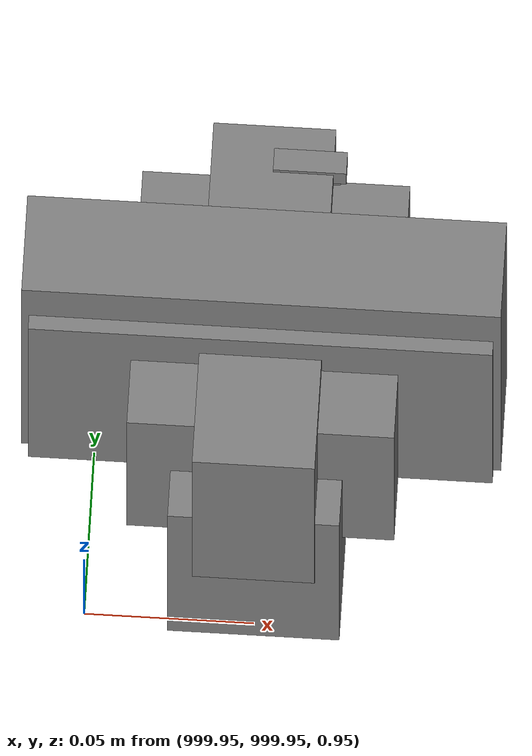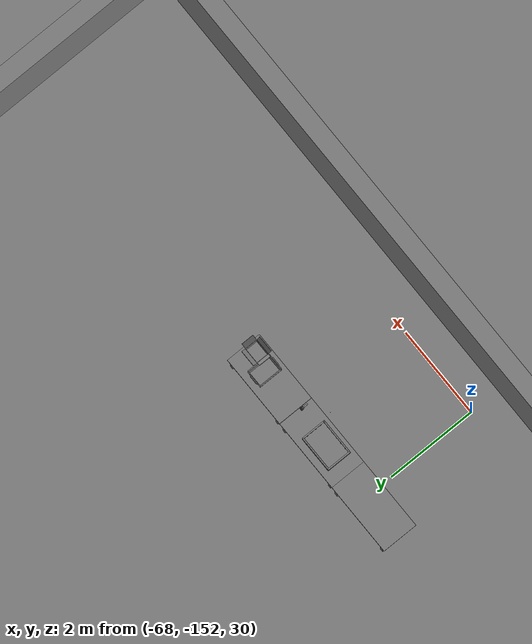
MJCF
<mujoco>
    <option gravity="0.000000000 0.000000000 -9.810000420" timestep="0.0049999999" integrator="implicitfast" density="1.225" viscosity="1.8000001e-05" noslip_iterations="10" iterations="100" sdf_iterations="50">
        <flag multiccd="disable"/>
    </option>
    <size memory="1000M"/>
    <compiler coordinate="local"/>
    <worldbody>
        <light cutoff="30" pos="0 1 1" dir="0 -1 -2"/>
        <light cutoff="30" pos="0 -1 1" dir="0 1 -2"/>
        <body pos="-64.866622925 -149.383972168 30.183746338" euler="89.999984741 89.999946594 0.000000000" name="openloong_gripper_2f85_fix_base_usda_bluebox_01">
            <geom contype="1" conaffinity="1" density="1000" type="box" material="" rgba="0.500000000 0.500000000 0.500000000 1.000000000" solimp="0.899999976 0.949999988 0.001000000" friction="1.000000000 0.005000000 0.000100000" solref="0.020000000 1.000000000" margin="0" condim="3" group="0" pos="0.276580811 0.187225342 0.000068665" quat="0.707106948 0.000077471 0.707106352 0.000077486" size="0.100000001 0.057999998 0.010000000" name="openloong_gripper_2f85_fix_base_usda_geom_2115B572_9238_43DA_8007_C7434E9026B9"/>
            <geom contype="1" conaffinity="1" density="1000" type="box" material="" rgba="0.500000000 0.500000000 0.500000000 1.000000000" solimp="0.899999976 0.949999988 0.001000000" friction="1.000000000 0.005000000 0.000100000" solref="0.020000000 1.000000000" margin="0" condim="3" group="0" pos="0.000000000 0.002883911 0.000000000" quat="0.999999881 0.000000000 0.000000000 0.000000000" size="0.254000008 0.003000000 0.172000006" name="openloong_gripper_2f85_fix_base_usda_geom_6CA94200_20A2_4347_9B67_9B2FF977F712"/>
            <geom contype="1" conaffinity="1" density="1000" type="box" material="" rgba="0.500000000 0.500000000 0.500000000 1.000000000" solimp="0.899999976 0.949999988 0.001000000" friction="1.000000000 0.005000000 0.000100000" solref="0.020000000 1.000000000" margin="0" condim="3" group="0" pos="0.000000000 0.124874115 0.173484802" quat="0.999796331 0.020176515 -0.000000015 0.000000030" size="0.259999990 0.119999997 0.007000000" name="openloong_gripper_2f85_fix_base_usda_geom_D4F133B9_49B0_4A10_824D_6F308057BB7D"/>
            <geom contype="1" conaffinity="1" density="1000" type="box" material="" rgba="0.500000000 0.500000000 0.500000000 1.000000000" solimp="0.899999976 0.949999988 0.001000000" friction="1.000000000 0.005000000 0.000100000" solref="0.020000000 1.000000000" margin="0" condim="3" group="0" pos="0.000000000 0.124874115 -0.173469543" quat="0.999796331 -0.020176545 -0.000000015 0.000000000" size="0.259999990 0.119999997 0.007000000" name="openloong_gripper_2f85_fix_base_usda_geom_52B77472_569C_4F8F_B2B0_1E22D7987282"/>
            <geom contype="1" conaffinity="1" density="1000" type="box" material="" rgba="0.500000000 0.500000000 0.500000000 1.000000000" solimp="0.899999976 0.949999988 0.001000000" friction="1.000000000 0.005000000 0.000100000" solref="0.020000000 1.000000000" margin="0" condim="3" group="0" pos="0.000000000 0.214008331 0.188980103" quat="0.999912977 0.013176724 0.000000015 0.000000000" size="0.259999990 0.029999999 0.012500000" name="openloong_gripper_2f85_fix_base_usda_geom_51A61016_F2E4_45EE_A85B_951B8A7EC35C"/>
            <geom contype="1" conaffinity="1" density="1000" type="box" material="" rgba="0.500000000 0.500000000 0.500000000 1.000000000" solimp="0.899999976 0.949999988 0.001000000" friction="1.000000000 0.005000000 0.000100000" solref="0.020000000 1.000000000" margin="0" condim="3" group="0" pos="-0.258361816 0.125289917 0.001876831" quat="0.702796936 -0.020792112 0.710783124 0.020769298" size="0.189999998 0.119999997 0.009000000" name="openloong_gripper_2f85_fix_base_usda_geom_2468D21F_C843_4028_A122_60BDD9817ACB"/>
            <geom contype="1" conaffinity="1" density="1000" type="box" material="" rgba="0.500000000 0.500000000 0.500000000 1.000000000" solimp="0.899999976 0.949999988 0.001000000" friction="1.000000000 0.005000000 0.000100000" solref="0.020000000 1.000000000" margin="0" condim="3" group="0" pos="0.000000000 0.214008331 -0.188980103" quat="0.999912977 -0.013176769 0.000000030 0.000000015" size="0.259999990 0.029999999 0.012500000" name="openloong_gripper_2f85_fix_base_usda_geom_D2A52157_104D_4AAA_9F61_439976CB13F4"/>
            <geom contype="1" conaffinity="1" density="1000" type="box" material="" rgba="0.500000000 0.500000000 0.500000000 1.000000000" solimp="0.899999976 0.949999988 0.001000000" friction="1.000000000 0.005000000 0.000100000" solref="0.020000000 1.000000000" margin="0" condim="3" group="0" pos="-0.276611328 0.187225342 0.000068665" quat="0.707106650 0.000077441 0.707106709 0.000077456" size="0.100000001 0.057999998 0.010000000" name="openloong_gripper_2f85_fix_base_usda_geom_158FDC34_1563_4585_BE96_04155A1F73B6"/>
            <geom contype="1" conaffinity="1" density="1000" type="box" material="" rgba="0.500000000 0.500000000 0.500000000 1.000000000" solimp="0.899999976 0.949999988 0.001000000" friction="1.000000000 0.005000000 0.000100000" solref="0.020000000 1.000000000" margin="0" condim="3" group="0" pos="0.258331299 0.125289917 0.001876831" quat="0.702851415 0.018856421 0.710823774 -0.019329369" size="0.189999998 0.119999997 0.009000000" name="openloong_gripper_2f85_fix_base_usda_geom_4B5E1284_AED0_46FC_8505_43E4B075D997"/>
            <freejoint name="openloong_gripper_2f85_fix_base_usda_bluebox_01_joint"/>
            <site size="0.005000000 0.005000000 0.005000000" rgba="0.500000000 0.500000000 0.500000000 1.000000000" pos="0.000000000 0.000000000 0.000000000" quat="0.999961913 0.008726534 0.000000000 0.000000000" group="0" type="sphere" name="openloong_gripper_2f85_fix_base_usda_bluebox_01site"/>
        </body>
        <body pos="-64.496299744 -149.491867065 30.235729218" euler="0.000000000 0.000000000 89.999946594" name="openloong_gripper_2f85_fix_base_usda_cardboardbox_01">
            <geom contype="1" conaffinity="1" density="1000" type="box" material="" rgba="0.500000000 0.500000000 0.500000000 1.000000000" solimp="0.899999976 0.949999988 0.001000000" friction="1.000000000 0.005000000 0.000100000" solref="0.020000000 1.000000000" margin="0" condim="3" group="0" pos="-0.003166199 -0.004086494 0.005052090" quat="1.000000000 0.000000000 0.000000000 0.000000000" size="0.142499998 0.177500010 0.005000000" name="openloong_gripper_2f85_fix_base_usda_geom_044C3530_FA00_4719_AD89_E52E789E730E"/>
            <geom contype="1" conaffinity="1" density="1000" type="box" material="" rgba="0.500000000 0.500000000 0.500000000 1.000000000" solimp="0.899999976 0.949999988 0.001000000" friction="1.000000000 0.005000000 0.000100000" solref="0.020000000 1.000000000" margin="0" condim="3" group="0" pos="-0.003166199 0.170316696 0.150570869" quat="1.000000000 0.000000000 0.000000000 0.000000000" size="0.142499998 0.005000000 0.149999991" name="openloong_gripper_2f85_fix_base_usda_geom_3516DD66_7D8E_40EF_8CE0_431B323A8C87"/>
            <geom contype="1" conaffinity="1" density="1000" type="box" material="" rgba="0.500000000 0.500000000 0.500000000 1.000000000" solimp="0.899999976 0.949999988 0.001000000" friction="1.000000000 0.005000000 0.000100000" solref="0.020000000 1.000000000" margin="0" condim="3" group="0" pos="-0.147399902 -0.005307198 0.150570869" quat="1.000000000 0.000000000 0.000000000 0.000000000" size="0.005000000 0.177500010 0.149999991" name="openloong_gripper_2f85_fix_base_usda_geom_94B3EE22_A5F4_4EE6_B9CA_A58B60D217EB"/>
            <geom contype="1" conaffinity="1" density="1000" type="box" material="" rgba="0.500000000 0.500000000 0.500000000 1.000000000" solimp="0.899999976 0.949999988 0.001000000" friction="1.000000000 0.005000000 0.000100000" solref="0.020000000 1.000000000" margin="0" condim="3" group="0" pos="0.140275955 -0.005307198 0.150570869" quat="1.000000000 0.000000000 0.000000000 0.000000000" size="0.005000000 0.177500010 0.149999991" name="openloong_gripper_2f85_fix_base_usda_geom_F16B631E_2BEB_4B77_AF63_B32BE0457B4C"/>
            <geom contype="1" conaffinity="1" density="1000" type="box" material="" rgba="0.500000000 0.500000000 0.500000000 1.000000000" solimp="0.899999976 0.949999988 0.001000000" friction="1.000000000 0.005000000 0.000100000" solref="0.020000000 1.000000000" margin="0" condim="3" group="0" pos="-0.003166199 -0.181550980 0.150570869" quat="1.000000000 0.000000000 0.000000000 0.000000000" size="0.142499998 0.005000000 0.149999991" name="openloong_gripper_2f85_fix_base_usda_geom_D7948DB9_67CC_4990_9283_00BC2731DDC2"/>
            <freejoint name="openloong_gripper_2f85_fix_base_usda_cardboardbox_01_joint"/>
            <site size="0.005000000 0.005000000 0.005000000" rgba="0.500000000 0.500000000 0.500000000 1.000000000" pos="0.000000000 0.000000000 0.000000000" quat="0.999961913 0.008726535 0.000000000 0.000000000" group="0" type="sphere" name="openloong_gripper_2f85_fix_base_usda_site_14EFBA15_8542_474A_A5B3_BD890EDF080A"/>
            <body pos="0.139160156 -0.004048347 0.301930904" euler="-179.999954224 49.383502960 179.999954224" name="openloong_gripper_2f85_fix_base_usda_A1_006">
                <geom contype="1" conaffinity="1" density="1000" type="box" material="" rgba="0.500000000 0.500000000 0.500000000 1.000000000" solimp="0.899999976 0.949999988 0.001000000" friction="1.000000000 0.005000000 0.000100000" solref="0.020000000 1.000000000" margin="0" condim="3" group="0" pos="-0.071587563 0.000009537 0.001745224" quat="0.999999881 0.000000000 0.000000000 0.000000000" size="0.071249999 0.179999992 0.002500000" name="openloong_gripper_2f85_fix_base_usda_geom_B8795C08_A276_49FF_91BA_26E2A6B40CDB"/>
                <joint armature="0" stiffness="0.07" damping="0.0099999998" axis="0.000000 1.000000 0.000000" type="hinge" name="openloong_gripper_2f85_fix_base_usda_A1_006"/>
            </body>
            <body pos="-0.145902634 -0.004086494 0.301938057" euler="-180.000000000 -60.000011444 -180.000000000" name="openloong_gripper_2f85_fix_base_usda_A2_006">
                <geom contype="1" conaffinity="1" density="1000" type="box" material="" rgba="0.500000000 0.500000000 0.500000000 1.000000000" solimp="0.899999976 0.949999988 0.001000000" friction="1.000000000 0.005000000 0.000100000" solref="0.020000000 1.000000000" margin="0" condim="3" group="0" pos="0.071268082 0.000009537 0.002717972" quat="0.000002921 0.000000000 -0.000000030 0.999999881" size="0.071249999 0.179999992 0.002500000" name="openloong_gripper_2f85_fix_base_usda_geom_FFF5E416_0E59_4E1B_B5FD_D20FF97EC07C"/>
                <joint armature="0" stiffness="0.07" damping="0.0099999998" axis="0.000000 1.000000 0.000000" type="hinge" name="openloong_gripper_2f85_fix_base_usda_A2_006"/>
            </body>
            <body pos="-0.003385544 0.175991058 0.301930904" euler="-125.858116150 -0.000004561 0.000002331" name="openloong_gripper_2f85_fix_base_usda_B2_006">
                <geom contype="1" conaffinity="1" density="1000" type="box" material="" rgba="0.500000000 0.500000000 0.500000000 1.000000000" solimp="0.899999976 0.949999988 0.001000000" friction="1.000000000 0.005000000 0.000100000" solref="0.020000000 1.000000000" margin="0" condim="3" group="0" pos="0.000009537 -0.070939064 -0.002470016" quat="0.999614120 0.027776197 -0.000000015 0.000000030" size="0.137500003 0.064999998 0.005000000" name="openloong_gripper_2f85_fix_base_usda_geom_1208C060_D1A4_4813_AA41_16895E7D9663"/>
                <joint armature="0" stiffness="0.07" damping="0.0099999998" axis="1.000000 0.000000 0.000000" type="hinge" name="openloong_gripper_2f85_fix_base_usda_B2_006"/>
            </body>
            <body pos="-0.003385544 -0.184140205 0.301938057" euler="147.805557251 0.000000000 0.000000000" name="openloong_gripper_2f85_fix_base_usda_B1_006">
                <geom contype="1" conaffinity="1" density="1000" type="box" material="" rgba="0.500000000 0.500000000 0.500000000 1.000000000" solimp="0.899999976 0.949999988 0.001000000" friction="1.000000000 0.005000000 0.000100000" solref="0.020000000 1.000000000" margin="0" condim="3" group="0" pos="-0.000028610 0.070202351 -0.002703667" quat="0.999614179 -0.027776167 0.000000000 0.000000000" size="0.137500003 0.064999998 0.005000000" name="openloong_gripper_2f85_fix_base_usda_geom_F6FFBA55_B3DE_48DA_A112_A9D558A745AF"/>
                <joint armature="0" stiffness="0.07" damping="0.0099999998" axis="1.000000 0.000000 0.000000" type="hinge" name="openloong_gripper_2f85_fix_base_usda_B1_006"/>
            </body>
        </body>
        <body pos="-65.882858276 -149.481979370 30.229999542" euler="-64.487716675 0.000000000 0.000000000" name="openloong_gripper_2f85_fix_base_usda_Barcode">
            <geom contype="1" conaffinity="1" density="1000" type="box" material="" rgba="0.500000000 0.500000000 0.500000000 1.000000000" solimp="0.899999976 0.949999988 0.001000000" friction="1.000000000 0.005000000 0.000100000" solref="0.020000000 1.000000000" margin="0" condim="3" group="0" pos="0.000000000 0.013038635 0.001419067" quat="0.000000000 0.000000000 0.000000000 1.000000119" size="0.034000002 0.010000000 0.017999999" name="openloong_gripper_2f85_fix_base_usda_geom_D5E50EEC_A3BA_46BB_971E_F46D68590AEB"/>
            <geom contype="1" conaffinity="1" density="1000" type="box" material="" rgba="0.500000000 0.500000000 0.500000000 1.000000000" solimp="0.899999976 0.949999988 0.001000000" friction="1.000000000 0.005000000 0.000100000" solref="0.020000000 1.000000000" margin="0" condim="3" group="0" pos="0.000000000 -0.035301208 -0.007095337" quat="0.000000000 0.000000000 -0.043619365 0.999048233" size="0.028999999 0.010000000 0.020000000" name="openloong_gripper_2f85_fix_base_usda_geom_D6B93E81_9873_4BBC_AFAB_EC6C84575DC3"/>
            <geom contype="1" conaffinity="1" density="1000" type="box" material="" rgba="0.500000000 0.500000000 0.500000000 1.000000000" solimp="0.899999976 0.949999988 0.001000000" friction="1.000000000 0.005000000 0.000100000" solref="0.020000000 1.000000000" margin="0" condim="3" group="0" pos="0.000000000 -0.043411255 -0.011749268" quat="0.922262907 0.386563420 0.000000000 0.000000000" size="0.026000001 0.010000000 0.020000000" name="openloong_gripper_2f85_fix_base_usda_geom_8F7BCF95_17B3_412D_B660_A873CD15C252"/>
            <geom contype="1" conaffinity="1" density="1000" type="box" material="" rgba="0.500000000 0.500000000 0.500000000 1.000000000" solimp="0.899999976 0.949999988 0.001000000" friction="1.000000000 0.005000000 0.000100000" solref="0.020000000 1.000000000" margin="0" condim="3" group="0" pos="0.000000000 -0.016967773 -0.031860352" quat="0.000000000 0.000000000 0.000000000 1.000000119" size="0.008000000 0.010000000 0.013000000" name="openloong_gripper_2f85_fix_base_usda_geom_29A897CB_15F4_4B46_9D57_2A7D7B2E7763"/>
            <geom contype="1" conaffinity="1" density="1000" type="box" material="" rgba="0.500000000 0.500000000 0.500000000 1.000000000" solimp="0.899999976 0.949999988 0.001000000" friction="1.000000000 0.005000000 0.000100000" solref="0.020000000 1.000000000" margin="0" condim="3" group="0" pos="0.000000000 -0.001869202 0.000312805" quat="0.953716993 0.300705761 0.000000000 0.000000000" size="0.032000002 0.010000000 0.018999999" name="openloong_gripper_2f85_fix_base_usda_geom_1284A075_FC0C_4FD2_9FA6_FE650C241A78"/>
            <geom contype="1" conaffinity="1" density="1000" type="box" material="" rgba="0.500000000 0.500000000 0.500000000 1.000000000" solimp="0.899999976 0.949999988 0.001000000" friction="1.000000000 0.005000000 0.000100000" solref="0.020000000 1.000000000" margin="0" condim="3" group="0" pos="0.000000000 -0.019531250 -0.003173828" quat="0.953716993 0.300705761 0.000000000 0.000000000" size="0.030999999 0.010000000 0.020000000" name="openloong_gripper_2f85_fix_base_usda_geom_DD42D017_F559_40C4_8A2E_E7F1ACAC2CA2"/>
            <geom contype="1" conaffinity="1" density="1000" type="box" material="" rgba="0.500000000 0.500000000 0.500000000 1.000000000" solimp="0.899999976 0.949999988 0.001000000" friction="1.000000000 0.005000000 0.000100000" solref="0.020000000 1.000000000" margin="0" condim="3" group="0" pos="0.000000000 -0.035301208 -0.007095337" quat="0.953716993 0.300705761 0.000000000 0.000000000" size="0.028999999 0.010000000 0.020000000" name="openloong_gripper_2f85_fix_base_usda_geom_286840FB_CA11_43E4_98B2_BEC088D5C1FD"/>
            <geom contype="1" conaffinity="1" density="1000" type="box" material="" rgba="0.500000000 0.500000000 0.500000000 1.000000000" solimp="0.899999976 0.949999988 0.001000000" friction="1.000000000 0.005000000 0.000100000" solref="0.020000000 1.000000000" margin="0" condim="3" group="0" pos="0.000000000 -0.042617798 -0.071121216" quat="0.000000000 0.000000000 0.000000000 1.000000119" size="0.013000000 0.021000000 0.059999999" name="openloong_gripper_2f85_fix_base_usda_geom_D4B533BB_6159_445E_BD56_EF05949C7888"/>
            <freejoint name="openloong_gripper_2f85_fix_base_usda_Barcode_joint"/>
            <site size="0.005000000 0.005000000 0.005000000" rgba="0.500000000 0.500000000 0.500000000 1.000000000" pos="0.000000000 0.000000000 0.000000000" quat="1.000000000 0.000000000 0.000000000 0.000000000" group="0" type="sphere" name="openloong_gripper_2f85_fix_base_usda_Barcode_site"/>
        </body>
        <body pos="-66.745018005 -149.392349243 30.184000015" euler="0.000000000 0.000000000 89.999946594" name="[22333049120971]_Basket_01">
            <geom contype="1" conaffinity="1" density="1000" type="box" material="" rgba="0.500000000 0.500000000 0.500000000 1.000000000" solimp="0.899999976 0.949999988 0.001000000" friction="1.000000000 0.005000000 0.000100000" solref="0.020000000 1.000000000" margin="0" condim="3" group="0" pos="-0.052425385 0.389207840 0.089787483" quat="0.707107008 0.000000000 0.000000000 0.707106411" size="0.014249999 0.014249999 0.059999999" name="[22333049120971]_geom_91A5A519_9504_4DF0_917D_E0D2D085B7F0"/>
            <geom contype="1" conaffinity="1" density="1000" type="box" material="" rgba="0.500000000 0.500000000 0.500000000 1.000000000" solimp="0.899999976 0.949999988 0.001000000" friction="1.000000000 0.005000000 0.000100000" solref="0.020000000 1.000000000" margin="0" condim="3" group="0" pos="0.264015198 -0.133043289 0.089787483" quat="0.707107008 0.000000000 0.000000000 0.707106411" size="0.014249999 0.014249999 0.059999999" name="[22333049120971]_geom_8DBE7925_5D8C_400F_9BEF_4C5E191E9787"/>
            <geom contype="1" conaffinity="1" density="1000" type="box" material="" rgba="0.500000000 0.500000000 0.500000000 1.000000000" solimp="0.899999976 0.949999988 0.001000000" friction="1.000000000 0.005000000 0.000100000" solref="0.020000000 1.000000000" margin="0" condim="3" group="0" pos="-0.264015198 -0.265548706 0.089793205" quat="0.707107008 0.000000000 0.000000000 0.707106411" size="0.014249999 0.014249999 0.059999999" name="[22333049120971]_geom_A331D671_2597_43DD_873A_36FC428728C4"/>
            <geom contype="1" conaffinity="1" density="1000" type="box" material="" rgba="0.500000000 0.500000000 0.500000000 1.000000000" solimp="0.899999976 0.949999988 0.001000000" friction="1.000000000 0.005000000 0.000100000" solref="0.020000000 1.000000000" margin="0" condim="3" group="0" pos="-0.160263062 -0.389322281 0.089793205" quat="0.707107008 0.000000000 0.000000000 0.707106411" size="0.014249999 0.014249999 0.059999999" name="[22333049120971]_geom_4AD029B7_6248_44ED_9A7F_F099A4CE9853"/>
            <geom contype="1" conaffinity="1" density="1000" type="box" material="" rgba="0.500000000 0.500000000 0.500000000 1.000000000" solimp="0.899999976 0.949999988 0.001000000" friction="1.000000000 0.005000000 0.000100000" solref="0.020000000 1.000000000" margin="0" condim="3" group="0" pos="0.162265778 -0.389322281 0.089787483" quat="0.707107008 0.000000000 0.000000000 0.707106411" size="0.014249999 0.014249999 0.059999999" name="[22333049120971]_geom_00FB556F_5393_496E_82D7_E9E0FE875387"/>
            <geom contype="1" conaffinity="1" density="1000" type="box" material="" rgba="0.500000000 0.500000000 0.500000000 1.000000000" solimp="0.899999976 0.949999988 0.001000000" friction="1.000000000 0.005000000 0.000100000" solref="0.020000000 1.000000000" margin="0" condim="3" group="0" pos="0.264015198 0.389207840 0.089787483" quat="0.707107008 0.000000000 0.000000000 0.707106411" size="0.014249999 0.014249999 0.059999999" name="[22333049120971]_geom_B4DE7352_0216_4AC9_8D69_F0CBBF27182B"/>
            <geom contype="1" conaffinity="1" density="1000" type="box" material="" rgba="0.500000000 0.500000000 0.500000000 1.000000000" solimp="0.899999976 0.949999988 0.001000000" friction="1.000000000 0.005000000 0.000100000" solref="0.020000000 1.000000000" margin="0" condim="3" group="0" pos="-0.264015198 -0.133043289 0.089793205" quat="0.707107008 0.000000000 0.000000000 0.707106411" size="0.014249999 0.014249999 0.059999999" name="[22333049120971]_geom_8BAC3179_1DF8_4093_8CE3_E93ADADD2437"/>
            <geom contype="1" conaffinity="1" density="1000" type="box" material="" rgba="0.500000000 0.500000000 0.500000000 1.000000000" solimp="0.899999976 0.949999988 0.001000000" friction="1.000000000 0.005000000 0.000100000" solref="0.020000000 1.000000000" margin="0" condim="3" group="0" pos="-0.264026642 0.269256592 0.089793205" quat="0.707107008 0.000000000 0.000000000 0.707106411" size="0.014249999 0.014249999 0.059999999" name="[22333049120971]_geom_79FDC776_153F_4A60_8886_31A55E33166C"/>
            <geom contype="1" conaffinity="1" density="1000" type="box" material="" rgba="0.500000000 0.500000000 0.500000000 1.000000000" solimp="0.899999976 0.949999988 0.001000000" friction="1.000000000 0.005000000 0.000100000" solref="0.020000000 1.000000000" margin="0" condim="3" group="0" pos="0.054462433 0.389207840 0.089787483" quat="0.707107008 0.000000000 0.000000000 0.707106411" size="0.014249999 0.014249999 0.059999999" name="[22333049120971]_geom_F5431842_7DA5_423F_8330_08B9D6487603"/>
            <geom contype="1" conaffinity="1" density="1000" type="box" material="" rgba="0.500000000 0.500000000 0.500000000 1.000000000" solimp="0.899999976 0.949999988 0.001000000" friction="1.000000000 0.005000000 0.000100000" solref="0.020000000 1.000000000" margin="0" condim="3" group="0" pos="0.054462433 -0.389322281 0.089787483" quat="0.707107008 0.000000000 0.000000000 0.707106411" size="0.014249999 0.014249999 0.059999999" name="[22333049120971]_geom_969F24A7_B8AB_419E_99FF_2A7A333D39B3"/>
            <geom contype="1" conaffinity="1" density="1000" type="box" material="" rgba="0.500000000 0.500000000 0.500000000 1.000000000" solimp="0.899999976 0.949999988 0.001000000" friction="1.000000000 0.005000000 0.000100000" solref="0.020000000 1.000000000" margin="0" condim="3" group="0" pos="0.264015198 0.269256592 0.089793205" quat="0.707107008 0.000000000 0.000000000 0.707106411" size="0.014249999 0.014249999 0.059999999" name="[22333049120971]_geom_BFFB89E4_25F3_48CF_8AFA_E61BA7A47EC1"/>
            <geom contype="1" conaffinity="1" density="1000" type="box" material="" rgba="0.500000000 0.500000000 0.500000000 1.000000000" solimp="0.899999976 0.949999988 0.001000000" friction="1.000000000 0.005000000 0.000100000" solref="0.020000000 1.000000000" margin="0" condim="3" group="0" pos="0.264015198 -0.389322281 0.089787483" quat="0.707107008 0.000000000 0.000000000 0.707106411" size="0.014249999 0.014249999 0.059999999" name="[22333049120971]_geom_3A0337FD_2EB7_4468_81C2_44A7535AE955"/>
            <geom contype="1" conaffinity="1" density="1000" type="box" material="" rgba="0.500000000 0.500000000 0.500000000 1.000000000" solimp="0.899999976 0.949999988 0.001000000" friction="1.000000000 0.005000000 0.000100000" solref="0.020000000 1.000000000" margin="0" condim="3" group="0" pos="0.000000000 0.000000000 0.015998840" quat="0.707107008 0.000000000 0.000000000 0.707106411" size="0.403499991 0.279000014 0.015750000" name="[22333049120971]_geom_9191A2DD_DE8E_42C0_A895_3BED645190A3"/>
            <geom contype="1" conaffinity="1" density="1000" type="box" material="" rgba="0.500000000 0.500000000 0.500000000 1.000000000" solimp="0.899999976 0.949999988 0.001000000" friction="1.000000000 0.005000000 0.000100000" solref="0.020000000 1.000000000" margin="0" condim="3" group="0" pos="0.000000000 -0.389476776 0.163619041" quat="0.707107008 0.000000000 0.000000000 0.707106411" size="0.015000000 0.277500004 0.015750000" name="[22333049120971]_geom_C096C8A8_DC6C_4FD6_8485_9C0447410AC7"/>
            <geom contype="1" conaffinity="1" density="1000" type="box" material="" rgba="0.500000000 0.500000000 0.500000000 1.000000000" solimp="0.899999976 0.949999988 0.001000000" friction="1.000000000 0.005000000 0.000100000" solref="0.020000000 1.000000000" margin="0" condim="3" group="0" pos="0.162265778 0.389207840 0.089787483" quat="0.707107008 0.000000000 0.000000000 0.707106411" size="0.014249999 0.014249999 0.059999999" name="[22333049120971]_geom_BFBF1790_A7FD_4A80_B743_1D20FF68EF24"/>
            <geom contype="1" conaffinity="1" density="1000" type="box" material="" rgba="0.500000000 0.500000000 0.500000000 1.000000000" solimp="0.899999976 0.949999988 0.001000000" friction="1.000000000 0.005000000 0.000100000" solref="0.020000000 1.000000000" margin="0" condim="3" group="0" pos="0.000000000 0.389471054 0.163619041" quat="0.707107008 0.000000000 0.000000000 0.707106411" size="0.015000000 0.277500004 0.015750000" name="[22333049120971]_geom_11D559DF_2BDE_4388_BE59_AE3F4BA56D49"/>
            <geom contype="1" conaffinity="1" density="1000" type="box" material="" rgba="0.500000000 0.500000000 0.500000000 1.000000000" solimp="0.899999976 0.949999988 0.001000000" friction="1.000000000 0.005000000 0.000100000" solref="0.020000000 1.000000000" margin="0" condim="3" group="0" pos="-0.263511658 0.000000000 0.163619041" quat="0.707107008 0.000000000 0.000000000 0.707106411" size="0.403499991 0.015000000 0.015750000" name="[22333049120971]_geom_FD1A7D67_AA0A_49E3_917B_32329EEA1B91"/>
            <geom contype="1" conaffinity="1" density="1000" type="box" material="" rgba="0.500000000 0.500000000 0.500000000 1.000000000" solimp="0.899999976 0.949999988 0.001000000" friction="1.000000000 0.005000000 0.000100000" solref="0.020000000 1.000000000" margin="0" condim="3" group="0" pos="-0.264015198 0.141334534 0.089793205" quat="0.707107008 0.000000000 0.000000000 0.707106411" size="0.014249999 0.014249999 0.059999999" name="[22333049120971]_geom_E5924455_2E3F_442C_951F_03651F90F5E3"/>
            <geom contype="1" conaffinity="1" density="1000" type="box" material="" rgba="0.500000000 0.500000000 0.500000000 1.000000000" solimp="0.899999976 0.949999988 0.001000000" friction="1.000000000 0.005000000 0.000100000" solref="0.020000000 1.000000000" margin="0" condim="3" group="0" pos="0.264015198 -0.265548706 0.089787483" quat="0.707107008 0.000000000 0.000000000 0.707106411" size="0.014249999 0.014249999 0.059999999" name="[22333049120971]_geom_250200E5_1C50_4108_A2DD_6EF7660059BA"/>
            <geom contype="1" conaffinity="1" density="1000" type="box" material="" rgba="0.500000000 0.500000000 0.500000000 1.000000000" solimp="0.899999976 0.949999988 0.001000000" friction="1.000000000 0.005000000 0.000100000" solref="0.020000000 1.000000000" margin="0" condim="3" group="0" pos="-0.160263062 0.389207840 0.089787483" quat="0.707107008 0.000000000 0.000000000 0.707106411" size="0.014249999 0.014249999 0.059999999" name="[22333049120971]_geom_0B267E62_976A_4483_84CF_BF03120DA957"/>
            <geom contype="1" conaffinity="1" density="1000" type="box" material="" rgba="0.500000000 0.500000000 0.500000000 1.000000000" solimp="0.899999976 0.949999988 0.001000000" friction="1.000000000 0.005000000 0.000100000" solref="0.020000000 1.000000000" margin="0" condim="3" group="0" pos="-0.052425385 -0.389322281 0.089787483" quat="0.707107008 0.000000000 0.000000000 0.707106411" size="0.014249999 0.014249999 0.059999999" name="[22333049120971]_geom_E35DD751_8DE4_4F3A_AB96_D394FB3AF75A"/>
            <geom contype="1" conaffinity="1" density="1000" type="box" material="" rgba="0.500000000 0.500000000 0.500000000 1.000000000" solimp="0.899999976 0.949999988 0.001000000" friction="1.000000000 0.005000000 0.000100000" solref="0.020000000 1.000000000" margin="0" condim="3" group="0" pos="-0.264026642 -0.389322281 0.089793205" quat="0.707107008 0.000000000 0.000000000 0.707106411" size="0.014249999 0.014249999 0.059999999" name="[22333049120971]_geom_8931D11F_0A97_47A0_BF4A_CCF51F683859"/>
            <geom contype="1" conaffinity="1" density="1000" type="box" material="" rgba="0.500000000 0.500000000 0.500000000 1.000000000" solimp="0.899999976 0.949999988 0.001000000" friction="1.000000000 0.005000000 0.000100000" solref="0.020000000 1.000000000" margin="0" condim="3" group="0" pos="0.264015198 0.141334534 0.089787483" quat="0.707107008 0.000000000 0.000000000 0.707106411" size="0.014249999 0.014249999 0.059999999" name="[22333049120971]_geom_836C3740_2EAC_45CE_9FEB_B48F0ED67A41"/>
            <geom contype="1" conaffinity="1" density="1000" type="box" material="" rgba="0.500000000 0.500000000 0.500000000 1.000000000" solimp="0.899999976 0.949999988 0.001000000" friction="1.000000000 0.005000000 0.000100000" solref="0.020000000 1.000000000" margin="0" condim="3" group="0" pos="-0.264015198 0.389207840 0.089793205" quat="0.707107008 0.000000000 0.000000000 0.707106411" size="0.014249999 0.014249999 0.059999999" name="[22333049120971]_geom_0A0CA267_4B19_45B2_AF9C_56439BE40863"/>
            <geom contype="1" conaffinity="1" density="1000" type="box" material="" rgba="0.500000000 0.500000000 0.500000000 1.000000000" solimp="0.899999976 0.949999988 0.001000000" friction="1.000000000 0.005000000 0.000100000" solref="0.020000000 1.000000000" margin="0" condim="3" group="0" pos="0.264015198 0.004480362 0.089787483" quat="0.707107008 0.000000000 0.000000000 0.707106411" size="0.014249999 0.014249999 0.059999999" name="[22333049120971]_geom_412439DD_00AA_4F27_8AF8_5C81757D3926"/>
            <geom contype="1" conaffinity="1" density="1000" type="box" material="" rgba="0.500000000 0.500000000 0.500000000 1.000000000" solimp="0.899999976 0.949999988 0.001000000" friction="1.000000000 0.005000000 0.000100000" solref="0.020000000 1.000000000" margin="0" condim="3" group="0" pos="0.263694763 -0.000011444 0.163619041" quat="0.707107008 0.000000000 0.000000000 0.707106411" size="0.403499991 0.015000000 0.015750000" name="[22333049120971]_geom_FAAB8A01_B04A_4294_A97F_21C32DE3E591"/>
            <geom contype="1" conaffinity="1" density="1000" type="box" material="" rgba="0.500000000 0.500000000 0.500000000 1.000000000" solimp="0.899999976 0.949999988 0.001000000" friction="1.000000000 0.005000000 0.000100000" solref="0.020000000 1.000000000" margin="0" condim="3" group="0" pos="-0.264015198 0.004480362 0.089793205" quat="0.707107008 0.000000000 0.000000000 0.707106411" size="0.014249999 0.014249999 0.059999999" name="[22333049120971]_geom_77091061_E27C_4AD2_A161_248A8310FC69"/>
            <freejoint name="[22333049120971]_joint_7AED667C_03CF_48DD_8E2A_E5F02DCC1699"/>
        </body>
        <body pos="0.000000000 0.000000000 0.000000000" euler="0.000000000 0.000000000 0.000000000" name="Static Objects_Static Objects">
            <geom contype="1" conaffinity="1" density="1000" type="box" material="" rgba="0.500000000 0.500000000 0.500000000 1.000000000" solimp="0.899999976 0.949999988 0.001000000" friction="1.000000000 0.005000000 0.000100000" solref="0.020000000 1.000000000" margin="0" condim="3" group="0" pos="-67.544113159 -149.365814209 29.727830887" quat="0.500000417 0.499999970 0.499999553 0.499999970" size="0.381000012 0.319999993 0.041000001" name="Static Objects_geom_7B963C7A_4173_4D8B_A696_79EE2C7718BE"/>
            <geom contype="1" conaffinity="1" density="1000" type="box" material="" rgba="0.500000000 0.500000000 0.500000000 1.000000000" solimp="0.899999976 0.949999988 0.001000000" friction="1.000000000 0.005000000 0.000100000" solref="0.020000000 1.000000000" margin="0" condim="3" group="0" pos="-68.239501953 -149.365814209 30.086868286" quat="0.500000417 0.499999970 0.499999553 0.499999970" size="0.370999992 0.039500002 0.745000005" name="Static Objects_geom_D1C95465_E19F_4C19_A685_0774C265909C"/>
            <geom contype="1" conaffinity="1" density="1000" type="box" material="" rgba="0.500000000 0.500000000 0.500000000 1.000000000" solimp="0.899999976 0.949999988 0.001000000" friction="1.000000000 0.005000000 0.000100000" solref="0.020000000 1.000000000" margin="0" condim="3" group="0" pos="-68.239501953 -149.365814209 30.147235870" quat="0.500000417 0.499999970 0.499999553 0.499999970" size="0.400000006 0.022000000 0.800000012" name="Static Objects_geom_9947417A_61A2_4A23_A686_31E8A0680968"/>
            <geom contype="1" conaffinity="1" density="1000" type="box" material="" rgba="0.500000000 0.500000000 0.500000000 1.000000000" solimp="0.899999976 0.949999988 0.001000000" friction="1.000000000 0.005000000 0.000100000" solref="0.020000000 1.000000000" margin="0" condim="3" group="0" pos="-68.934890747 -149.365814209 29.727830887" quat="0.500000417 0.499999970 0.499999553 0.499999970" size="0.381000012 0.319999993 0.041000001" name="Static Objects_geom_ECE8A062_A7FE_4467_9ABA_296BD5C5B873"/>
            <geom contype="1" conaffinity="1" density="1000" type="box" material="" rgba="0.500000000 0.500000000 0.500000000 1.000000000" solimp="0.899999976 0.949999988 0.001000000" friction="1.000000000 0.005000000 0.000100000" solref="0.020000000 1.000000000" margin="0" condim="3" group="0" pos="-68.239501953 -149.365814209 29.561563492" quat="0.500000417 0.499999970 0.499999553 0.499999970" size="0.020000000 0.022000000 0.660000026" name="Static Objects_geom_9C6C1F98_6BA3_4040_A8C3_173D2C2A345F"/>
            <geom contype="1" conaffinity="1" density="1000" type="box" material="" rgba="0.500000000 0.500000000 0.500000000 1.000000000" solimp="0.899999976 0.949999988 0.001000000" friction="1.000000000 0.005000000 0.000100000" solref="0.020000000 1.000000000" margin="0" condim="3" group="0" pos="-65.945671082 -149.365814209 29.727830887" quat="0.500000417 0.499999970 0.499999553 0.499999970" size="0.381000012 0.319999993 0.041000001" name="Static Objects_geom_7148089E_38B0_4F49_9408_914A3E4BA02D"/>
            <geom contype="1" conaffinity="1" density="1000" type="box" material="" rgba="0.500000000 0.500000000 0.500000000 1.000000000" solimp="0.899999976 0.949999988 0.001000000" friction="1.000000000 0.005000000 0.000100000" solref="0.020000000 1.000000000" margin="0" condim="3" group="0" pos="-66.641059875 -149.365814209 30.086868286" quat="0.500000417 0.499999970 0.499999553 0.499999970" size="0.370999992 0.039500002 0.745000005" name="Static Objects_geom_0DA09655_774A_45BE_BA7E_917E73584EAF"/>
            <geom contype="1" conaffinity="1" density="1000" type="box" material="" rgba="0.500000000 0.500000000 0.500000000 1.000000000" solimp="0.899999976 0.949999988 0.001000000" friction="1.000000000 0.005000000 0.000100000" solref="0.020000000 1.000000000" margin="0" condim="3" group="0" pos="-66.641059875 -149.365814209 30.147235870" quat="0.500000417 0.499999970 0.499999553 0.499999970" size="0.400000006 0.022000000 0.800000012" name="Static Objects_geom_3F502A11_F6AF_4038_95FE_2232054AAF37"/>
            <geom contype="1" conaffinity="1" density="1000" type="box" material="" rgba="0.500000000 0.500000000 0.500000000 1.000000000" solimp="0.899999976 0.949999988 0.001000000" friction="1.000000000 0.005000000 0.000100000" solref="0.020000000 1.000000000" margin="0" condim="3" group="0" pos="-67.336448669 -149.365814209 29.727830887" quat="0.500000417 0.499999970 0.499999553 0.499999970" size="0.381000012 0.319999993 0.041000001" name="Static Objects_geom_24551D82_BCEC_4F9F_A6BB_C53CD34EBBD6"/>
            <geom contype="1" conaffinity="1" density="1000" type="box" material="" rgba="0.500000000 0.500000000 0.500000000 1.000000000" solimp="0.899999976 0.949999988 0.001000000" friction="1.000000000 0.005000000 0.000100000" solref="0.020000000 1.000000000" margin="0" condim="3" group="0" pos="-66.641059875 -149.365814209 29.561563492" quat="0.500000417 0.499999970 0.499999553 0.499999970" size="0.020000000 0.022000000 0.660000026" name="Static Objects_geom_365FAF20_8B3E_43E3_B33C_9B7CFA853414"/>
            <geom contype="1" conaffinity="1" density="1000" type="box" material="" rgba="0.500000000 0.500000000 0.500000000 1.000000000" solimp="0.899999976 0.949999988 0.001000000" friction="1.000000000 0.005000000 0.000100000" solref="0.020000000 1.000000000" margin="0" condim="3" group="0" pos="-64.338577271 -149.365814209 29.727830887" quat="0.500000417 0.499999970 0.499999553 0.499999970" size="0.381000012 0.319999993 0.041000001" name="Static Objects_geom_74D4C985_8827_4492_9D4C_BFD1FF74C30E"/>
            <geom contype="1" conaffinity="1" density="1000" type="box" material="" rgba="0.500000000 0.500000000 0.500000000 1.000000000" solimp="0.899999976 0.949999988 0.001000000" friction="1.000000000 0.005000000 0.000100000" solref="0.020000000 1.000000000" margin="0" condim="3" group="0" pos="-65.033966064 -149.365814209 30.086868286" quat="0.500000417 0.499999970 0.499999553 0.499999970" size="0.370999992 0.039500002 0.745000005" name="Static Objects_geom_0C0BD1F5_4B7E_47C1_A9C7_3B3093D72554"/>
            <geom contype="1" conaffinity="1" density="1000" type="box" material="" rgba="0.500000000 0.500000000 0.500000000 1.000000000" solimp="0.899999976 0.949999988 0.001000000" friction="1.000000000 0.005000000 0.000100000" solref="0.020000000 1.000000000" margin="0" condim="3" group="0" pos="-65.033966064 -149.365814209 30.147235870" quat="0.500000417 0.499999970 0.499999553 0.499999970" size="0.400000006 0.022000000 0.800000012" name="Static Objects_geom_6A783FDB_DA02_4029_A6F0_2F7F9A733989"/>
            <geom contype="1" conaffinity="1" density="1000" type="box" material="" rgba="0.500000000 0.500000000 0.500000000 1.000000000" solimp="0.899999976 0.949999988 0.001000000" friction="1.000000000 0.005000000 0.000100000" solref="0.020000000 1.000000000" margin="0" condim="3" group="0" pos="-65.729354858 -149.365814209 29.727830887" quat="0.500000417 0.499999970 0.499999553 0.499999970" size="0.381000012 0.319999993 0.041000001" name="Static Objects_geom_082E86CF_9C51_4CA7_A226_3166C819C692"/>
            <geom contype="1" conaffinity="1" density="1000" type="box" material="" rgba="0.500000000 0.500000000 0.500000000 1.000000000" solimp="0.899999976 0.949999988 0.001000000" friction="1.000000000 0.005000000 0.000100000" solref="0.020000000 1.000000000" margin="0" condim="3" group="0" pos="-65.033966064 -149.365814209 29.561563492" quat="0.500000417 0.499999970 0.499999553 0.499999970" size="0.020000000 0.022000000 0.660000026" name="Static Objects_geom_BCBA4F18_27A3_46BB_AADA_6F1D3E1FB4A5"/>
            <geom contype="1" conaffinity="1" density="1000" type="box" material="" rgba="0.500000000 0.500000000 0.500000000 1.000000000" solimp="0.899999976 0.949999988 0.001000000" friction="1.000000000 0.005000000 0.000100000" solref="0.020000000 1.000000000" margin="0" condim="3" group="0" pos="-61.754566193 -137.853729248 33.906845093" quat="0.707107067 0.000000000 0.000000000 0.707106471" size="0.759999990 0.759999990 4.500000000" name="Static Objects_geom_C2CB6056_5F8C_40A3_B2D4_D07058620267"/>
            <geom contype="1" conaffinity="1" density="1000" type="box" material="" rgba="0.500000000 0.500000000 0.500000000 1.000000000" solimp="0.899999976 0.949999988 0.001000000" friction="1.000000000 0.005000000 0.000100000" solref="0.020000000 1.000000000" margin="0" condim="3" group="0" pos="-57.511135101 -144.927108765 31.707921982" quat="1.000000000 0.000000000 0.000000000 0.000000000" size="0.200000003 8.000000000 2.299999952" name="Static Objects_geom_77698236_7D1C_40DE_85D3_07A1FDBE4952"/>
            <geom contype="1" conaffinity="1" density="1000" type="box" material="" rgba="0.500000000 0.500000000 0.500000000 1.000000000" solimp="0.899999976 0.949999988 0.001000000" friction="1.000000000 0.005000000 0.000100000" solref="0.020000000 1.000000000" margin="0" condim="3" group="0" pos="-80.517646790 -157.574050903 31.688196182" quat="0.707107067 0.000000000 0.000000000 0.707106471" size="0.600000024 0.600000024 2.299999952" name="Static Objects_geom_714AB638_23FF_4AB4_B063_542B99948C1D"/>
            <geom contype="1" conaffinity="1" density="1000" type="box" material="" rgba="0.500000000 0.500000000 0.500000000 1.000000000" solimp="0.899999976 0.949999988 0.001000000" friction="1.000000000 0.005000000 0.000100000" solref="0.020000000 1.000000000" margin="0" condim="3" group="0" pos="-80.711044312 -147.414932251 31.666158676" quat="1.000000000 0.000000000 0.000000000 0.000000000" size="0.200000003 10.000000000 2.299999952" name="Static Objects_geom_2EA399B2_90B6_46B0_A0EB_7D4141A87DA2"/>
            <geom contype="1" conaffinity="1" density="1000" type="box" material="" rgba="0.500000000 0.500000000 0.500000000 1.000000000" solimp="0.899999976 0.949999988 0.001000000" friction="1.000000000 0.005000000 0.000100000" solref="0.020000000 1.000000000" margin="0" condim="3" group="0" pos="-57.687217712 -137.434692383 31.688196182" quat="0.707107067 0.000000000 0.000000000 0.707106471" size="0.600000024 0.600000024 2.299999952" name="Static Objects_geom_AFBFF1BE_5C5D_4934_9A8E_59EAEC908CBA"/>
            <geom contype="1" conaffinity="1" density="1000" type="box" material="" rgba="0.500000000 0.500000000 0.500000000 1.000000000" solimp="0.899999976 0.949999988 0.001000000" friction="1.000000000 0.005000000 0.000100000" solref="0.020000000 1.000000000" margin="0" condim="3" group="0" pos="-69.537033081 -140.263229370 31.714921951" quat="0.707107067 0.000000000 0.000000000 0.707106471" size="0.759999990 4.500000000 2.299999952" name="Static Objects_geom_9CE2191E_A187_477E_9709_302586A6260C"/>
            <geom contype="1" conaffinity="1" density="1000" type="box" material="" rgba="0.500000000 0.500000000 0.500000000 1.000000000" solimp="0.899999976 0.949999988 0.001000000" friction="1.000000000 0.005000000 0.000100000" solref="0.020000000 1.000000000" margin="0" condim="3" group="0" pos="-80.073638916 -137.853713989 33.906845093" quat="0.707107067 0.000000000 0.000000000 0.707106471" size="0.759999990 0.759999990 4.500000000" name="Static Objects_geom_071AB146_7068_442D_8275_0CF760226E82"/>
            <geom contype="1" conaffinity="1" density="1000" type="box" material="" rgba="0.500000000 0.500000000 0.500000000 1.000000000" solimp="0.899999976 0.949999988 0.001000000" friction="1.000000000 0.005000000 0.000100000" solref="0.020000000 1.000000000" margin="0" condim="3" group="0" pos="-73.406707764 -155.734664917 31.707921982" quat="1.000000000 0.000000000 0.000000000 0.000000000" size="0.200000003 3.000000000 2.299999952" name="Static Objects_geom_5F32DDC4_5FCB_4036_A027_5F9F5E0E91CF"/>
            <geom contype="1" conaffinity="1" density="1000" type="box" material="" rgba="0.500000000 0.500000000 0.500000000 1.000000000" solimp="0.899999976 0.949999988 0.001000000" friction="1.000000000 0.005000000 0.000100000" solref="0.020000000 1.000000000" margin="0" condim="3" group="0" pos="-68.497543335 -137.448257446 31.707921982" quat="0.707107067 0.000000000 0.000000000 0.707106471" size="0.200000003 14.000000000 2.299999952" name="Static Objects_geom_64D194B7_08D7_407D_A0D1_2509E6CAEA9C"/>
            <geom contype="1" conaffinity="1" density="1000" type="cylinder" material="" rgba="0.500000000 0.500000000 0.500000000 1.000000000" solimp="0.899999976 0.949999988 0.001000000" friction="1.000000000 0.005000000 0.000100000" solref="0.020000000 1.000000000" margin="0" condim="3" group="0" pos="-68.868522644 -142.134506226 31.711090088" quat="0.707107067 0.000000000 0.000000000 0.707106471" size="0.509999990 2.299999952 1.000000000" name="Static Objects_geom_306E5EBF_B0C9_4ABC_AD90_924C8BCE664C"/>
            <geom contype="1" conaffinity="1" density="1000" type="plane" material="" rgba="0.500000000 0.500000000 0.500000000 1.000000000" solimp="0.899999976 0.949999988 0.001000000" friction="1.000000000 0.005000000 0.000100000" solref="0.020000000 1.000000000" margin="0" condim="3" group="0" pos="-72.873703003 -147.131927490 29.409669876" quat="1.000000000 0.000000000 0.000000000 0.000000000" size="18.000000000 14.000000000 1.000000000" name="Static Objects_geom_B171E1A9_6545_4C04_974E_DEB7A2CF43EE"/>
            <geom contype="1" conaffinity="1" density="1000" type="box" material="" rgba="0.500000000 0.500000000 0.500000000 1.000000000" solimp="0.899999976 0.949999988 0.001000000" friction="1.000000000 0.005000000 0.000100000" solref="0.020000000 1.000000000" margin="0" condim="3" group="0" pos="-79.943580627 -157.782272339 31.707921982" quat="0.707107067 0.000000000 0.000000000 0.707106471" size="0.200000003 7.000000000 2.299999952" name="Static Objects_geom_016CBC11_38A3_46C9_9264_F41208C5906D"/>
            <geom contype="1" conaffinity="1" density="1000" type="box" material="" rgba="0.500000000 0.500000000 0.500000000 1.000000000" solimp="0.899999976 0.949999988 0.001000000" friction="1.000000000 0.005000000 0.000100000" solref="0.020000000 1.000000000" margin="0" condim="3" group="0" pos="-65.421028137 -152.903442383 31.707921982" quat="0.707107067 0.000000000 0.000000000 0.707106471" size="0.200000003 7.800000191 2.299999952" name="Static Objects_geom_D8EBFCED_B315_4BC0_96FA_E8395B6CF2E2"/>
            <geom contype="1" conaffinity="1" density="1000" type="box" material="" rgba="0.500000000 0.500000000 0.500000000 1.000000000" solimp="0.899999976 0.949999988 0.001000000" friction="1.000000000 0.005000000 0.000100000" solref="0.020000000 1.000000000" margin="0" condim="3" group="0" pos="-74.776908875 -149.964416504 31.688196182" quat="1.000000000 0.000000000 0.000000000 0.000000000" size="0.600000024 0.409999996 2.299999952" name="Static Objects_geom_4A7FAE19_628E_40C0_B7DC_C4E306EFBC0E"/>
            <geom contype="1" conaffinity="1" density="1000" type="cylinder" material="" rgba="0.500000000 0.500000000 0.500000000 1.000000000" solimp="0.899999976 0.949999988 0.001000000" friction="1.000000000 0.005000000 0.000100000" solref="0.020000000 1.000000000" margin="0" condim="3" group="0" pos="-60.161884308 -142.134506226 31.711090088" quat="0.707107067 0.000000000 0.000000000 0.707106471" size="0.509999990 2.299999952 1.000000000" name="Static Objects_geom_98470492_56BE_42FD_9610_DC9732B98486"/>
            <geom contype="1" conaffinity="1" density="1000" type="cylinder" material="" rgba="0.500000000 0.500000000 0.500000000 1.000000000" solimp="0.899999976 0.949999988 0.001000000" friction="1.000000000 0.005000000 0.000100000" solref="0.020000000 1.000000000" margin="0" condim="3" group="0" pos="-75.382453918 -149.963455200 31.711090088" quat="0.707107067 0.000000000 0.000000000 0.707106471" size="0.409999996 2.299999952 1.000000000" name="Static Objects_geom_49A632FB_8179_47E5_B669_F8F7103D89EF"/>
            <geom contype="1" conaffinity="1" density="1000" type="cylinder" material="" rgba="0.500000000 0.500000000 0.500000000 1.000000000" solimp="0.899999976 0.949999988 0.001000000" friction="1.000000000 0.005000000 0.000100000" solref="0.020000000 1.000000000" margin="0" condim="3" group="0" pos="-74.154960632 -149.963455200 31.711090088" quat="0.707107067 0.000000000 0.000000000 0.707106471" size="0.409999996 2.299999952 1.000000000" name="Static Objects_geom_C8AD3DC0_12B8_4F88_93CA_FDBDB1FC45A2"/>
            <geom contype="1" conaffinity="1" density="1000" type="cylinder" material="" rgba="0.500000000 0.500000000 0.500000000 1.000000000" solimp="0.899999976 0.949999988 0.001000000" friction="1.000000000 0.005000000 0.000100000" solref="0.020000000 1.000000000" margin="0" condim="3" group="0" pos="-77.566612244 -142.134506226 31.711090088" quat="0.707107067 0.000000000 0.000000000 0.707106471" size="0.509999990 2.299999952 1.000000000" name="Static Objects_geom_C94D14BD_338F_4752_9609_C1097ACE8D48"/>
        </body>
        <body pos="1000.000000000 999.999938965 1.000000000" euler="0.000000000 0.000000000 180.000000000" name="openloong_gripper_2f85_fix_base_usda_intelcore_i5">
            <geom contype="1" conaffinity="1" density="1000" type="box" material="" rgba="0.500000000 0.500000000 0.500000000 1.000000000" solimp="0.899999976 0.949999988 0.001000000" friction="1.000000000 0.005000000 0.000100000" solref="0.020000000 1.000000000" margin="0" condim="3" group="0" pos="0.000000000 0.000000000 0.051722717" quat="0.707106709 0.000000000 0.000000000 -0.707106769" size="0.052800000 0.018080002 0.052800000" name="openloong_gripper_2f85_fix_base_usda_geom_D0DEE0BC_CC3F_4949_B74E_F8DAE1E5BC68"/>
            <freejoint name="openloong_gripper_2f85_fix_base_usda_intelcore_i5_joint"/>
            <site size="0.005000000 0.005000000 0.005000000" rgba="0.500000000 0.500000000 0.500000000 1.000000000" pos="0.000000000 0.000000000 0.000000000" quat="0.999961913 0.008726534 0.000000000 0.000000000" group="0" type="sphere" name="openloong_gripper_2f85_fix_base_usda_intelcore_i5site"/>
        </body>
        <body pos="1000.000000000 1000.000000000 1.000000000" euler="0.000000000 0.000000000 180.000000000" name="openloong_gripper_2f85_fix_base_usda_wifi_box">
            <geom contype="1" conaffinity="1" density="1000" type="box" material="" rgba="0.500000000 0.500000000 0.500000000 1.000000000" solimp="0.899999976 0.949999988 0.001000000" friction="1.000000000 0.005000000 0.000100000" solref="0.020000000 1.000000000" margin="0" condim="3" group="0" pos="0.000000000 0.000000000 0.058978677" quat="0.000000000 0.000000047 0.000000000 1.000000000" size="0.068499997 0.018999999 0.059000000" name="openloong_gripper_2f85_fix_base_usda_geom_70343F17_AF63_404A_A069_1BA8FC6F8CBE"/>
            <freejoint name="openloong_gripper_2f85_fix_base_usda_wifi_box_joint"/>
            <site size="0.005000000 0.005000000 0.005000000" rgba="0.500000000 0.500000000 0.500000000 1.000000000" pos="0.000000000 0.000000000 0.000000000" quat="0.999961913 0.008726500 0.000000000 0.000000000" group="0" type="sphere" name="openloong_gripper_2f85_fix_base_usda_wifi_boxsite"/>
        </body>
        <body pos="1000.000000000 1000.000000000 1.000000000" euler="0.000011953 0.000005123 -179.999984741" name="openloong_gripper_2f85_fix_base_usda_intel_box">
            <geom contype="1" conaffinity="1" density="1000" type="box" material="" rgba="0.500000000 0.500000000 0.500000000 1.000000000" solimp="0.899999976 0.949999988 0.001000000" friction="1.000000000 0.005000000 0.000100000" solref="0.020000000 1.000000000" margin="0" condim="3" group="0" pos="0.000000000 -0.000067139 0.000082284" quat="0.707106709 0.000000225 0.000000253 0.707106650" size="0.052800003 0.025300000 0.052800003" name="openloong_gripper_2f85_fix_base_usda_geom_136A334E_3011_450B_B362_51D575E8087B"/>
            <freejoint name="openloong_gripper_2f85_fix_base_usda_intel_box_joint"/>
            <site size="0.005000000 0.005000000 0.005000000" rgba="0.500000000 0.500000000 0.500000000 1.000000000" pos="0.000000000 0.000000000 0.000000000" quat="0.999961913 0.008726500 0.000000000 0.000000000" group="0" type="sphere" name="openloong_gripper_2f85_fix_base_usda_intel_boxsite"/>
        </body>
        <body pos="1000.000000000 1000.000000000 1.000000000" euler="0.000000000 0.000000000 180.000000000" name="openloong_gripper_2f85_fix_base_usda_cpu_fan">
            <geom contype="1" conaffinity="1" density="1000" type="box" material="" rgba="0.500000000 0.500000000 0.500000000 1.000000000" solimp="0.899999976 0.949999988 0.001000000" friction="1.000000000 0.005000000 0.000100000" solref="0.020000000 1.000000000" margin="0" condim="3" group="0" pos="0.000000000 0.000000000 0.070034981" quat="0.000000000 0.000000000 0.000000000 1.000000000" size="0.070700005 0.014699999 0.070700005" name="openloong_gripper_2f85_fix_base_usda_geom_E00E999A_6046_4A7A_828F_3DB93C4374D8"/>
            <freejoint name="openloong_gripper_2f85_fix_base_usda_cpu_fan_joint"/>
            <site size="0.005000000 0.005000000 0.005000000" rgba="0.500000000 0.500000000 0.500000000 1.000000000" pos="0.000000000 0.000000000 0.000000000" quat="0.999961913 0.008726535 0.000000000 0.000000000" group="0" type="sphere" name="openloong_gripper_2f85_fix_base_usda_cpu_fancsite"/>
        </body>
        <body pos="1000.000000000 1000.000000000 1.000000000" euler="0.000000000 0.000000000 180.000000000" name="openloong_gripper_2f85_fix_base_usda_battery_01">
            <geom contype="1" conaffinity="1" density="1000" type="box" material="" rgba="0.500000000 0.500000000 0.500000000 1.000000000" solimp="0.899999976 0.949999988 0.001000000" friction="1.000000000 0.005000000 0.000100000" solref="0.020000000 1.000000000" margin="0" condim="3" group="0" pos="-0.011123657 -0.041940309 0.101691343" quat="1.000000000 0.000000000 0.000000000 0.000000000" size="0.010800000 0.003375000 0.004725000" name="openloong_gripper_2f85_fix_base_usda_geom_A9DE9806_E323_4ACF_AEEE_A8BFC875805A"/>
            <geom contype="1" conaffinity="1" density="1000" type="box" material="" rgba="0.500000000 0.500000000 0.500000000 1.000000000" solimp="0.899999976 0.949999988 0.001000000" friction="1.000000000 0.005000000 0.000100000" solref="0.020000000 1.000000000" margin="0" condim="3" group="0" pos="-0.010876465 -0.044247437 0.047066893" quat="0.998702705 -0.050920475 0.000000000 0.000000000" size="0.009450001 0.002700000 0.024975000" name="openloong_gripper_2f85_fix_base_usda_geom_4363C9D9_5655_4CF0_B855_49D26156FB06"/>
            <geom contype="1" conaffinity="1" density="1000" type="box" material="" rgba="0.500000000 0.500000000 0.500000000 1.000000000" solimp="0.899999976 0.949999988 0.001000000" friction="1.000000000 0.005000000 0.000100000" solref="0.020000000 1.000000000" margin="0" condim="3" group="0" pos="-0.001235962 -0.000659180 0.047381196" quat="1.000000000 0.000000000 0.000000000 0.000000000" size="0.039420001 0.039150000 0.047250003" name="openloong_gripper_2f85_fix_base_usda_geom_F1AA3570_60D2_46CE_A77B_F2793AB8A84E"/>
            <geom contype="1" conaffinity="1" density="1000" type="box" material="" rgba="0.500000000 0.500000000 0.500000000 1.000000000" solimp="0.899999976 0.949999988 0.001000000" friction="1.000000000 0.005000000 0.000100000" solref="0.020000000 1.000000000" margin="0" condim="3" group="0" pos="-0.010876465 -0.039138794 0.009851727" quat="1.000000000 0.000000000 0.000000000 0.000000000" size="0.009450001 0.010800000 0.013500000" name="openloong_gripper_2f85_fix_base_usda_geom_28AB3288_E3C6_45D2_91D4_1496F17931E2"/>
            <geom contype="1" conaffinity="1" density="1000" type="box" material="" rgba="0.500000000 0.500000000 0.500000000 1.000000000" solimp="0.899999976 0.949999988 0.001000000" friction="1.000000000 0.005000000 0.000100000" solref="0.020000000 1.000000000" margin="0" condim="3" group="0" pos="-0.010876465 -0.041528322 0.071508206" quat="1.000000000 0.000000000 0.000000000 0.000000000" size="0.009450001 0.002700000 0.027000001" name="openloong_gripper_2f85_fix_base_usda_geom_8BE6F2FD_542D_4918_B088_88028A4F9C12"/>
            <freejoint name="openloong_gripper_2f85_fix_base_usda_battery_01_joint"/>
            <site size="0.005000000 0.005000000 0.005000000" rgba="0.500000000 0.500000000 0.500000000 1.000000000" pos="0.000000000 0.000000000 0.000000000" quat="0.999961913 0.008726500 0.000000000 0.000000000" group="0" type="sphere" name="openloong_gripper_2f85_fix_base_usda_battery_01site"/>
        </body>
        <body pos="-66.364105225 -149.540542603 31.170862198" euler="14.472659111 39.076728821 -110.588500977" mocap="true" name="spotlight1_SpotLight"/>
        <body pos="-65.889198303 -149.055541992 31.163034439" euler="117.027770996 9.953572273 148.693176270" mocap="true" name="spotlight2_SpotLight"/>
        <body pos="-66.364158630 -149.394958496 31.163312912" euler="42.996665955 -81.778701782 -154.073776245" mocap="true" name="spotlight4_SpotLight"/>
        <body pos="-66.291030884 -149.869689941 29.018842697" euler="0.000000000 0.000000000 89.999946594" mocap="true" name="openloong_gripper_2f85_fix_base_usda_leftHandMocap"/>
        <body pos="-66.291030884 -149.869689941 29.018842697" euler="0.000000000 0.000000000 89.999946594" mocap="true" name="openloong_gripper_2f85_fix_base_usda_rightHandMocap"/>
        <body pos="-66.291030884 -149.869689941 30.218843460" euler="0.000000000 0.000000000 89.999946594" name="openloong_gripper_2f85_fix_base_usda_base_link">
            <geom contype="1" conaffinity="1" density="1000" type="mesh" material="" rgba="0.783999979 0.783999979 0.783999979 1.000000000" solimp="0.899999976 0.949999988 0.001000000" friction="1.000000000 0.005000000 0.000100000" solref="0.020000000 1.000000000" margin="0" condim="3" group="3" mesh="base_link" pos="0.000000000 0.000000000 0.000000000" quat="1.000000000 0.000000000 0.000000000 0.000000000" size="1.000000000 1.000000000 1.000000000" name="openloong_gripper_2f85_fix_base_usda__geom_7_047EF977_3BB0_43D3_846B_2971A86E4994"/>
            <site size="0.005000000 0.005000000 0.005000000" rgba="0.500000000 0.500000000 0.500000000 1.000000000" pos="0.000000000 0.000000000 0.000000000" quat="1.000000000 0.000000000 0.000000000 0.000000000" group="0" type="sphere" name="openloong_gripper_2f85_fix_base_usda_imu"/>
            <inertial mass="22.447001" pos="-0.005664100 -0.001336700 0.238289997" diaginertia="0.374352545 0.277180195 0.220617250" quat="0.999247074 0.035235517 -0.015086859 0.006023135"/>
            <body pos="0.000000000 0.000000000 0.299997330" euler="0.000000000 0.000000000 0.000000000" name="openloong_gripper_2f85_fix_base_usda_dummy_body">
                <geom contype="1" conaffinity="1" density="1000" type="sphere" material="" rgba="0.783999979 0.783999979 0.783999979 1.000000000" solimp="0.899999976 0.949999988 0.001000000" friction="1.000000000 0.005000000 0.000100000" solref="0.020000000 1.000000000" margin="0" condim="3" group="3" pos="0.000000000 0.000000000 0.000000000" quat="1.000000000 0.000000000 0.000000000 0.000000000" size="0.010000000 0.000000000 0.000000000" name="openloong_gripper_2f85_fix_base_usda__geom_8_BFDB421C_4EE4_4FB1_91FB_C0CD73972D2E"/>
                <joint armature="0.0099999998" stiffness="0" damping="0.1" axis="0.000000 0.000000 1.000000" type="hinge" name="openloong_gripper_2f85_fix_base_usda_dummy_joint"/>
                <site size="0.010000000 0.005000000 0.005000000" rgba="0.500000000 0.500000000 0.500000000 1.000000000" pos="0.000000000 0.000000000 0.000000000" quat="1.000000000 0.000000000 0.000000000 0.000000000" group="3" type="sphere" name="openloong_gripper_2f85_fix_base_usda_dummy_site"/>
            </body>
            <body pos="0.009002686 0.000000000 0.406400681" euler="0.000000000 0.000000000 0.000000000" name="openloong_gripper_2f85_fix_base_usda_Link_head_yaw">
                <geom contype="1" conaffinity="1" density="1000" type="mesh" material="" rgba="0.783999979 0.783999979 0.783999979 1.000000000" solimp="0.899999976 0.949999988 0.001000000" friction="1.000000000 0.005000000 0.000100000" solref="0.020000000 1.000000000" margin="0" condim="3" group="3" mesh="Link_head_yaw" pos="0.000000000 0.000000000 0.000000000" quat="1.000000000 0.000000000 0.000000000 0.000000000" size="1.000000000 1.000000000 1.000000000" name="openloong_gripper_2f85_fix_base_usda__geom_10_FB56630A_BDE9_4C17_A850_65306831C93D"/>
                <inertial mass="0.84249002" pos="0.000000000 -0.002081400 0.044801001" diaginertia="0.000700588 0.000629000 0.000553812" quat="0.706933022 -0.015675601 0.015677100 0.706933022"/>
                <body pos="0.000000000 -0.034599304 0.048500061" euler="0.000000000 0.000000000 0.000000000" name="openloong_gripper_2f85_fix_base_usda_Link_head_pitch">
                    <geom contype="1" conaffinity="1" density="1000" type="mesh" material="" rgba="0.783999979 0.783999979 0.783999979 1.000000000" solimp="0.899999976 0.949999988 0.001000000" friction="1.000000000 0.005000000 0.000100000" solref="0.020000000 1.000000000" margin="0" condim="3" group="3" mesh="Link_head_pitch" pos="0.000000000 0.000000000 0.000000000" quat="1.000000000 0.000000000 0.000000000 0.000000000" size="1.000000000 1.000000000 1.000000000" name="openloong_gripper_2f85_fix_base_usda__geom_12_F2DABE2B_CBC9_42E2_96D0_FF1C4BB60CB5"/>
                    <inertial mass="1.3943" pos="0.020569000 0.033004001 0.125000000" diaginertia="0.006381400 0.006289940 0.004481460" quat="0.973390222 0.008406822 0.228157058 0.019624906"/>
                    <body pos="0.000000000 0.029998779 0.000000000" euler="0.000000000 0.000000000 0.000000000" name="openloong_gripper_2f85_fix_base_usda_neck_center_body">
                        <site size="0.010000000 0.005000000 0.005000000" rgba="0.500000000 0.500000000 0.500000000 1.000000000" pos="0.000000000 0.000000000 0.000000000" quat="1.000000000 0.000000000 0.000000000 0.000000000" group="3" type="sphere" name="openloong_gripper_2f85_fix_base_usda_neck_center_site"/>
                        <body pos="0.020004272 0.000000000 0.149999619" euler="-0.000002229 39.998176575 -90.000205994" name="openloong_gripper_2f85_fix_base_usda_camera_head">
                            <site size="0.010000000 0.005000000 0.005000000" rgba="0.500000000 0.500000000 0.500000000 1.000000000" pos="0.000000000 0.000000000 0.000000000" quat="1.000000000 0.000000000 0.000000000 0.000000000" group="3" type="sphere" name="openloong_gripper_2f85_fix_base_usda_camera_head_site"/>
                        </body>
                    </body>
                </body>
            </body>
            <body pos="0.003997803 -0.161598206 0.392200470" euler="0.000000000 0.000000000 0.000000000" name="openloong_gripper_2f85_fix_base_usda_Link_arm_r_01">
                <geom contype="1" conaffinity="1" density="1000" type="mesh" material="" rgba="0.783999979 0.783999979 0.783999979 1.000000000" solimp="0.899999976 0.949999988 0.001000000" friction="1.000000000 0.005000000 0.000100000" solref="0.020000000 1.000000000" margin="0" condim="3" group="3" mesh="Link_arm_r_01" pos="0.000000000 0.000000000 0.000000000" quat="1.000000000 0.000000000 0.000000000 0.000000000" size="1.000000000 1.000000000 1.000000000" name="openloong_gripper_2f85_fix_base_usda__geom_14_CE0E28BD_E09F_4747_951C_0094236EFE42"/>
                <joint armature="0.0099999998" stiffness="0" damping="1" axis="0.000000 -1.000000 0.000000" limited="true" range="-170.000015259 170.000015259" type="hinge" name="openloong_gripper_2f85_fix_base_usda_J_arm_r_01"/>
                <inertial mass="0.75641" pos="0.004494600 -0.038293999 -0.000001874" diaginertia="0.000842990 0.000803050 0.000587120" quat="-0.000163502 0.707098067 0.000812463 0.707115054"/>
                <body pos="-0.041992188 -0.041000366 0.000000000" euler="0.000000000 0.000000000 0.000000000" name="openloong_gripper_2f85_fix_base_usda_Link_arm_r_02">
                    <geom contype="1" conaffinity="1" density="1000" type="mesh" material="" rgba="0.783999979 0.783999979 0.783999979 1.000000000" solimp="0.899999976 0.949999988 0.001000000" friction="1.000000000 0.005000000 0.000100000" solref="0.020000000 1.000000000" margin="0" condim="3" group="3" mesh="Link_arm_r_02" pos="0.000000000 0.000000000 0.000000000" quat="1.000000000 0.000000000 0.000000000 0.000000000" size="1.000000000 1.000000000 1.000000000" name="openloong_gripper_2f85_fix_base_usda__geom_16_98CB9ABD_96CE_489E_97C0_5946A2821413"/>
                    <joint armature="0.0099999998" stiffness="0" damping="1" axis="-1.000000 0.000000 0.000000" limited="true" range="-105.000244141 105.000244141" type="hinge" name="openloong_gripper_2f85_fix_base_usda_J_arm_r_02"/>
                    <inertial mass="0.98500001" pos="0.041999999 -0.067430697 0.000000000" diaginertia="0.002262690 0.001730990 0.001154020" quat="0.500000000 0.500000000 -0.500000000 0.500000000"/>
                    <body pos="0.041992188 -0.122596741 0.000000000" euler="0.000000000 0.000000000 0.000000000" name="openloong_gripper_2f85_fix_base_usda_Link_arm_r_03">
                        <geom contype="1" conaffinity="1" density="1000" type="mesh" material="" rgba="0.783999979 0.783999979 0.783999979 1.000000000" solimp="0.899999976 0.949999988 0.001000000" friction="1.000000000 0.005000000 0.000100000" solref="0.020000000 1.000000000" margin="0" condim="3" group="3" mesh="Link_arm_r_03" pos="0.000000000 0.000000000 0.000000000" quat="1.000000000 0.000000000 0.000000000 0.000000000" size="1.000000000 1.000000000 1.000000000" name="openloong_gripper_2f85_fix_base_usda__geom_18_C4A11323_EE6B_4FEF_8CF5_1EBC4C3752C5"/>
                        <joint armature="0.0099999998" stiffness="0" damping="1" axis="0.000000 -1.000000 0.000000" limited="true" range="-170.000015259 170.000015259" type="hinge" name="openloong_gripper_2f85_fix_base_usda_J_arm_r_03"/>
                        <inertial mass="0.95899999" pos="-0.001413580 -0.164663002 0.020757901" diaginertia="0.002101340 0.002064590 0.000754802" quat="0.560480952 0.454391927 -0.443732947 0.531497955"/>
                        <body pos="0.035293579 -0.177406311 0.023998260" euler="0.000000000 0.000000000 0.000000000" name="openloong_gripper_2f85_fix_base_usda_Link_arm_r_04">
                            <geom contype="1" conaffinity="1" density="1000" type="mesh" material="" rgba="0.783999979 0.783999979 0.783999979 1.000000000" solimp="0.899999976 0.949999988 0.001000000" friction="1.000000000 0.005000000 0.000100000" solref="0.020000000 1.000000000" margin="0" condim="3" group="3" mesh="Link_arm_r_04" pos="0.000000000 0.000000000 0.000000000" quat="1.000000000 0.000000000 0.000000000 0.000000000" size="1.000000000 1.000000000 1.000000000" name="openloong_gripper_2f85_fix_base_usda__geom_20_DC372380_C2DB_4B4A_A62E_1223296CDDFF"/>
                            <joint armature="0.0099999998" stiffness="0" damping="1" axis="-1.000000 0.000000 0.000000" limited="true" range="0.000000000 170.000015259" type="hinge" name="openloong_gripper_2f85_fix_base_usda_J_arm_r_04"/>
                            <inertial mass="0.60000002" pos="-0.038727000 -0.060766999 -0.021003000" diaginertia="0.001092610 0.000712422 0.000645102" quat="0.327701002 0.632602990 -0.467366993 0.523443997"/>
                            <body pos="-0.035293579 -0.103492737 -0.023998260" euler="0.000000000 0.000000000 0.000000000" name="openloong_gripper_2f85_fix_base_usda_Link_arm_r_05">
                                <geom contype="1" conaffinity="1" density="1000" type="mesh" material="" rgba="0.783999979 0.783999979 0.783999979 1.000000000" solimp="0.899999976 0.949999988 0.001000000" friction="1.000000000 0.005000000 0.000100000" solref="0.020000000 1.000000000" margin="0" condim="3" group="3" mesh="Link_arm_r_05" pos="0.000000000 0.000000000 0.000000000" quat="1.000000000 0.000000000 0.000000000 0.000000000" size="1.000000000 1.000000000 1.000000000" name="openloong_gripper_2f85_fix_base_usda__geom_22_576DFA44_0843_455A_B3A9_AC11B76928C8"/>
                                <joint armature="0.0099999998" stiffness="0" damping="1" axis="0.000000 -1.000000 0.000000" limited="true" range="-170.000015259 170.000015259" type="hinge" name="openloong_gripper_2f85_fix_base_usda_J_arm_r_05"/>
                                <inertial mass="0.68976003" pos="0.000032712 -0.068658002 -0.000111780" diaginertia="0.002522510 0.002411100 0.000448695" quat="0.707660973 0.706543028 -0.002603360 0.002470550"/>
                                <body pos="-0.026489258 -0.196502686 0.000000000" euler="0.000000000 0.000000000 0.000000000" name="openloong_gripper_2f85_fix_base_usda_Link_arm_r_06">
                                    <geom contype="1" conaffinity="1" density="1000" type="mesh" material="" rgba="0.783999979 0.783999979 0.783999979 1.000000000" solimp="0.899999976 0.949999988 0.001000000" friction="1.000000000 0.005000000 0.000100000" solref="0.020000000 1.000000000" margin="0" condim="3" group="3" mesh="Link_arm_r_06" pos="0.000000000 0.000000000 0.000000000" quat="1.000000000 0.000000000 0.000000000 0.000000000" size="1.000000000 1.000000000 1.000000000" name="openloong_gripper_2f85_fix_base_usda__geom_24_7FB6E56F_77DA_4DB4_A445_CD9F7CCE5EAF"/>
                                    <joint armature="0.0099999998" stiffness="0" damping="1" axis="1.000000 0.000000 0.000000" limited="true" range="-105.000244141 105.000244141" type="hinge" name="openloong_gripper_2f85_fix_base_usda_J_arm_r_06"/>
                                    <inertial mass="0.28" pos="0.026078001 -0.000000896 0.001663700" diaginertia="0.000156930 0.000145601 0.000104979" quat="0.707080841 0.001851080 0.001883810 0.707127810"/>
                                    <body pos="0.026489258 0.000000000 0.031799316" euler="0.000000000 0.000000000 0.000000000" name="openloong_gripper_2f85_fix_base_usda_Link_arm_r_07">
                                        <geom contype="1" conaffinity="1" density="1000" type="mesh" material="" rgba="0.783999979 0.783999979 0.783999979 1.000000000" solimp="0.899999976 0.949999988 0.001000000" friction="1.000000000 0.005000000 0.000100000" solref="0.020000000 1.000000000" margin="0" condim="3" group="3" mesh="Link_arm_r_07" pos="0.000000000 0.000000000 0.000000000" quat="1.000000000 0.000000000 0.000000000 0.000000000" size="1.000000000 1.000000000 1.000000000" name="openloong_gripper_2f85_fix_base_usda__geom_26_D8AF506D_B085_42C3_A747_DBAB2AF36D17"/>
                                        <joint armature="0.0099999998" stiffness="0" damping="1" axis="0.000000 0.000000 1.000000" limited="true" range="-60.000133514 60.000133514" type="hinge" name="openloong_gripper_2f85_fix_base_usda_J_arm_r_07"/>
                                        <inertial mass="0.61353999" pos="-0.007859000 -0.158170000 -0.027736001" diaginertia="0.003037610 0.002570910 0.000729379" quat="0.427542925 0.443532884 -0.553093910 0.560867906"/>
                                        <body pos="0.000000000 0.286994934 -0.270000458" euler="150.000350952 -0.000001649 -0.000000442" name="openloong_gripper_2f85_fix_base_usda_camera_wrist_r">
                                            <site size="0.010000000 0.005000000 0.005000000" rgba="0.500000000 0.500000000 0.500000000 1.000000000" pos="0.000000000 0.000000000 0.000000000" quat="1.000000000 0.000000000 0.000000000 0.000000000" group="3" type="sphere" name="openloong_gripper_2f85_fix_base_usda_camera_wrist_r_site"/>
                                        </body>
                                        <body pos="0.000000000 -0.220008850 -0.033002853" euler="0.000000000 0.000000000 179.999969482" name="openloong_gripper_2f85_fix_base_usda_ee_center_body_r">
                                            <site size="0.010000000 0.005000000 0.005000000" rgba="0.500000000 0.500000000 0.500000000 1.000000000" pos="0.000000000 0.000000000 0.000000000" quat="1.000000000 0.000000000 0.000000000 0.000000000" group="3" type="sphere" name="openloong_gripper_2f85_fix_base_usda_ee_center_site_r"/>
                                        </body>
                                        <body pos="0.000000000 -0.066001892 -0.031000137" euler="89.999984741 0.000000000 180.000000000" name="openloong_gripper_2f85_fix_base_usda_zbr_base_link">
                                            <geom contype="1" conaffinity="1" density="1000" type="mesh" material="" rgba="0.783999979 0.783999979 0.783999979 1.000000000" solimp="0.899999976 0.949999988 0.001000000" friction="1.000000000 0.005000000 0.000100000" solref="0.020000000 1.000000000" margin="0" condim="3" group="3" mesh="base" pos="0.000000000 0.000003815 -0.000007629" quat="1.000000000 0.000000000 0.000000000 0.000000000" size="1.000000238 1.000000238 1.000000238" name="openloong_gripper_2f85_fix_base_usda__geom_30_8CAB4710_833C_43DE_A59F_45D7B3BAC6CC"/>
                                            <inertial mass="0.77744102" pos="0.000000000 -0.000027039 0.035467502" diaginertia="0.000260285 0.000225381 0.000152708" quat="0.999998808 -0.001528488 0.000000000 0.000000000"/>
                                            <body pos="-0.030609138 0.004745484 0.065696731" euler="-89.999984741 -0.000000000 0.000000000" name="openloong_gripper_2f85_fix_base_usda_r_left_driver">
                                                <geom contype="1" conaffinity="1" density="1000" type="mesh" material="" rgba="0.783999979 0.783999979 0.783999979 1.000000000" solimp="0.899999976 0.949999988 0.001000000" friction="1.000000000 0.005000000 0.000100000" solref="0.020000000 1.000000000" margin="0" condim="3" group="3" mesh="driver" pos="0.030609138 0.054901138 -0.004699708" quat="0.707106829 0.707106709 0.000000000 -0.000000000" size="1.000000238 1.000000238 1.000000238" name="openloong_gripper_2f85_fix_base_usda__geom_32_9C0AAB61_50BB_4E85_8B4B_FC0B399D0709"/>
                                                <joint armature="0.0049999999" stiffness="0" damping="0.1" axis="0.000000 0.000000 1.000000" limited="true" range="0.000000000 51.566200256" type="hinge" name="openloong_gripper_2f85_fix_base_usda_r_left_driver_joint"/>
                                                <inertial mass="0.0089956298" pos="0.000000000 0.017754700 0.001073140" diaginertia="0.000001724 0.000001609 0.000000322" quat="0.681301236 0.732003212 0.000000000 0.000000000"/>
                                                <body pos="-0.031402595 0.004524232 -0.010200503" euler="0.000000000 0.000000000 180.000000000" name="openloong_gripper_2f85_fix_base_usda_r_left_coupler">
                                                    <geom contype="1" conaffinity="1" density="1000" type="mesh" material="" rgba="0.783999979 0.783999979 0.783999979 1.000000000" solimp="0.899999976 0.949999988 0.001000000" friction="1.000000000 0.005000000 0.000100000" solref="0.020000000 1.000000000" margin="0" condim="3" group="3" mesh="coupler" pos="-0.062011734 -0.050354015 0.005500795" quat="0.707106829 -0.707106709 0.000000000 -0.000000000" size="1.000000238 1.000000238 1.000000238" name="openloong_gripper_2f85_fix_base_usda__geom_34_B6A4FEEC_C715_40DC_9B7C_E7532EEFE3C1"/>
                                                    <inertial mass="0.0140974" pos="0.000000000 0.003012090 0.023217499" diaginertia="0.000004162 0.000003522 0.000000888" quat="0.705635548 -0.045590367 0.045590367 0.705635548"/>
                                                </body>
                                            </body>
                                            <body pos="-0.012695315 -0.012001040 0.072212234" euler="-89.999984741 -0.000000000 0.000000000" name="openloong_gripper_2f85_fix_base_usda_r_left_spring_link">
                                                <geom contype="1" conaffinity="1" density="1000" type="mesh" material="" rgba="0.783999979 0.783999979 0.783999979 1.000000000" solimp="0.899999976 0.949999988 0.001000000" friction="1.000000000 0.005000000 0.000100000" solref="0.020000000 1.000000000" margin="0" condim="3" group="3" mesh="spring_link" pos="0.012695315 0.061416641 0.012050631" quat="0.707106829 0.707106709 0.000000000 -0.000000000" size="1.000000238 1.000000238 1.000000238" name="openloong_gripper_2f85_fix_base_usda__geom_36_1DD5CAB8_959F_44AC_A780_775666C3AF05"/>
                                                <joint armature="0.001" stiffness="0.050000001" damping="0.00125" axis="0.000000 0.000000 1.000000" limited="true" range="-17.000000000 51.566200256" type="hinge" name="openloong_gripper_2f85_fix_base_usda_r_left_spring_link_joint"/>
                                                <inertial mass="0.0221642" pos="-0.000000009 0.018162400 0.021265799" diaginertia="0.000008969 0.000006717 0.000002639" quat="0.663403213 -0.244737089 0.244737089 0.663403213"/>
                                                <body pos="-0.038208015 -0.042503368 0.002950669" euler="180.000000000 0.000000000 -0.002185660" name="openloong_gripper_2f85_fix_base_usda_r_left_follower">
                                                    <geom contype="1" conaffinity="1" density="1000" type="mesh" material="" rgba="0.783999979 0.783999979 0.783999979 1.000000000" solimp="0.899999976 0.949999988 0.001000000" friction="1.000000000 0.005000000 0.000100000" solref="0.020000000 1.000000000" margin="0" condim="3" group="3" mesh="tongue" pos="0.050918590 -0.103920005 -0.009099962" quat="0.707106829 -0.707106709 0.000000030 0.000000030" size="1.000000238 1.000000238 1.000000238" name="openloong_gripper_2f85_fix_base_usda__geom_40_B5C2ED36_7741_4668_9528_AD1081C03D1A"/>
                                                    <geom contype="1" conaffinity="1" density="1000" type="mesh" material="" rgba="0.783999979 0.783999979 0.783999979 1.000000000" solimp="0.899999976 0.949999988 0.001000000" friction="1.000000000 0.005000000 0.000100000" solref="0.020000000 1.000000000" margin="0" condim="3" group="3" mesh="follower" pos="0.050918590 -0.103920005 -0.009099962" quat="0.707106829 -0.707106709 0.000000030 0.000000030" size="1.000000238 1.000000238 1.000000238" name="openloong_gripper_2f85_fix_base_usda__geom_39_A00FDBF6_1743_4D82_AA72_E8AB623148F4"/>
                                                    <joint armature="0.001" stiffness="0" damping="0.1" axis="0.000000 0.000000 1.000000" limited="true" range="-49.999961853 51.566200256" type="hinge" name="openloong_gripper_2f85_fix_base_usda_r_left_follower"/>
                                                    <inertial mass="0.0125222" pos="0.000000000 -0.011046000 0.012478600" diaginertia="0.000002674 0.000002456 0.000000602" quat="0.986436546 0.164143041 0.000000000 0.000000000"/>
                                                    <body pos="-0.037765510 -0.103912376 -0.009099962" euler="-89.999984741 0.000000000 0.000004829" name="openloong_gripper_2f85_fix_base_usda_r_left_pad">
                                                        <geom contype="1" conaffinity="1" density="1000" type="box" material="" rgba="0.550000012 0.550000012 0.550000012 1.000000000" solimp="0.949999988 0.990000010 0.001000000" friction="0.699999988 0.005000000 0.000100000" solref="0.020000000 1.000000000" margin="0" condim="3" group="3" mass="1e-06" pos="0.043243419 0.000003815 0.119995147" quat="0.999999881 0.000000000 0.000000000 0.000000000" size="0.002000001 0.011000003 0.009375002" name="openloong_gripper_2f85_fix_base_usda_r_left_pad1_15D21195_6D8B_4AE5_89E7_7AB899FBCD2D"/>
                                                        <geom contype="1" conaffinity="1" density="1000" type="box" material="" rgba="0.449999988 0.449999988 0.449999988 1.000000000" solimp="0.949999988 0.990000010 0.001000000" friction="0.600000024 0.005000000 0.000100000" solref="0.020000000 1.000000000" margin="0" condim="3" group="3" mass="1e-06" pos="0.043243419 0.000003815 0.138748199" quat="0.999999881 0.000000000 0.000000000 0.000000000" size="0.002000001 0.011000003 0.009375002" name="openloong_gripper_2f85_fix_base_usda_r_left_pad2_C080A1AC_C74A_4ED1_829E_556FE09919D3"/>
                                                    </body>
                                                </body>
                                            </body>
                                            <body pos="0.030593880 -0.004753114 0.065696731" euler="89.999984741 0.000000000 180.000000000" name="openloong_gripper_2f85_fix_base_usda_r_right_driver">
                                                <geom contype="1" conaffinity="1" density="1000" type="mesh" material="" rgba="0.783999979 0.783999979 0.783999979 1.000000000" solimp="0.899999976 0.949999988 0.001000000" friction="1.000000000 0.005000000 0.000100000" solref="0.020000000 1.000000000" margin="0" condim="3" group="3" mesh="driver" pos="0.030593880 0.054901138 -0.004699708" quat="0.707106829 0.707106709 0.000000000 0.000000000" size="1.000000238 1.000000238 1.000000238" name="openloong_gripper_2f85_fix_base_usda__geom_42_B4C72C01_1A29_4894_84E8_B6C9BD22E30F"/>
                                                <joint armature="0.0049999999" stiffness="0" damping="0.1" axis="0.000000 0.000000 1.000000" limited="true" range="0.000000000 51.566200256" type="hinge" name="openloong_gripper_2f85_fix_base_usda_r_right_driver_joint"/>
                                                <inertial mass="0.0089956298" pos="0.000000000 0.017754700 0.001073140" diaginertia="0.000001724 0.000001609 0.000000322" quat="0.681301236 0.732003212 0.000000000 0.000000000"/>
                                                <body pos="-0.031417854 0.004531861 -0.010202411" euler="0.000000000 0.000000000 180.000000000" name="openloong_gripper_2f85_fix_base_usda_r_right_coupler">
                                                    <geom contype="1" conaffinity="1" density="1000" type="mesh" material="" rgba="0.783999979 0.783999979 0.783999979 1.000000000" solimp="0.899999976 0.949999988 0.001000000" friction="1.000000000 0.005000000 0.000100000" solref="0.020000000 1.000000000" margin="0" condim="3" group="3" mesh="coupler" pos="-0.062042251 -0.050376903 0.005500795" quat="0.707106829 -0.707106709 0.000000000 0.000000000" size="1.000000238 1.000000238 1.000000238" name="openloong_gripper_2f85_fix_base_usda__geom_44_8A2AF4D2_E6A0_4DD1_ADA5_1ABDFCF6645A"/>
                                                    <inertial mass="0.0140974" pos="0.000000000 0.003012090 0.023217499" diaginertia="0.000004162 0.000003522 0.000000888" quat="0.705635548 -0.045590367 0.045590367 0.705635548"/>
                                                </body>
                                            </body>
                                            <body pos="0.012695315 0.011997226 0.072219864" euler="89.999984741 0.000000000 180.000000000" name="openloong_gripper_2f85_fix_base_usda_r_right_spring_link">
                                                <geom contype="1" conaffinity="1" density="1000" type="mesh" material="" rgba="0.783999979 0.783999979 0.783999979 1.000000000" solimp="0.899999976 0.949999988 0.001000000" friction="1.000000000 0.005000000 0.000100000" solref="0.020000000 1.000000000" margin="0" condim="3" group="3" mesh="spring_link" pos="0.012695315 0.061424270 0.012048724" quat="0.707106829 0.707106709 0.000000000 0.000000000" size="1.000000238 1.000000238 1.000000238" name="openloong_gripper_2f85_fix_base_usda__geom_46_672A72BF_65E1_4EAE_A0E3_DC41248B055B"/>
                                                <joint armature="0.001" stiffness="0.050000001" damping="0.00125" axis="0.000000 0.000000 1.000000" limited="true" range="-17.000000000 51.566200256" type="hinge" name="openloong_gripper_2f85_fix_base_usda_r_right_spring_link_joint"/>
                                                <inertial mass="0.0221642" pos="-0.000000009 0.018162400 0.021265799" diaginertia="0.000008969 0.000006717 0.000002639" quat="0.663403213 -0.244737089 0.244737089 0.663403213"/>
                                                <body pos="-0.038208015 -0.042495739 0.002950669" euler="180.000000000 0.000000000 0.000000000" name="openloong_gripper_2f85_fix_base_usda_r_right_follower">
                                                    <geom contype="1" conaffinity="1" density="1000" type="mesh" material="" rgba="0.783999979 0.783999979 0.783999979 1.000000000" solimp="0.899999976 0.949999988 0.001000000" friction="1.000000000 0.005000000 0.000100000" solref="0.020000000 1.000000000" margin="0" condim="3" group="3" mesh="follower" pos="0.050888073 -0.103927635 -0.009099962" quat="0.707106829 -0.707106709 0.000000000 0.000000000" size="1.000000238 1.000000238 1.000000238" name="openloong_gripper_2f85_fix_base_usda__geom_50_339C9C4A_D7D1_49E1_99D1_984312B41A6B"/>
                                                    <geom contype="1" conaffinity="1" density="1000" type="mesh" material="" rgba="0.783999979 0.783999979 0.783999979 1.000000000" solimp="0.899999976 0.949999988 0.001000000" friction="1.000000000 0.005000000 0.000100000" solref="0.020000000 1.000000000" margin="0" condim="3" group="3" mesh="tongue" pos="0.050888073 -0.103927635 -0.009099962" quat="0.707106829 -0.707106709 0.000000000 0.000000000" size="1.000000238 1.000000238 1.000000238" name="openloong_gripper_2f85_fix_base_usda__geom_49_8E258DD1_50A1_46B0_B4F4_893B38EFCCAA"/>
                                                    <joint armature="0.001" stiffness="0" damping="0.1" axis="0.000000 0.000000 1.000000" limited="true" range="-49.999961853 51.566200256" type="hinge" name="openloong_gripper_2f85_fix_base_usda_r_right_follower_joint"/>
                                                    <inertial mass="0.0125222" pos="0.000000000 -0.011046000 0.012478600" diaginertia="0.000002674 0.000002456 0.000000602" quat="0.986436546 0.164143041 0.000000000 0.000000000"/>
                                                    <body pos="-0.037811287 -0.103927635 -0.009099962" euler="-89.999984741 0.000000000 0.000000000" name="openloong_gripper_2f85_fix_base_usda_r_right_pad">
                                                        <geom contype="1" conaffinity="1" density="1000" type="box" material="" rgba="0.449999988 0.449999988 0.449999988 1.000000000" solimp="0.949999988 0.990000010 0.001000000" friction="0.600000024 0.005000000 0.000100000" solref="0.020000000 1.000000000" margin="0" condim="3" group="3" mass="1e-06" pos="0.043258678 0.000000000 0.138748199" quat="1.000000000 0.000000000 0.000000000 0.000000000" size="0.002000001 0.011000003 0.009375002" name="openloong_gripper_2f85_fix_base_usda_r_right_pad2_A0BD9C2B_3B44_4B13_8AAF_16750F451459"/>
                                                        <geom contype="1" conaffinity="1" density="1000" type="box" material="" rgba="0.550000012 0.550000012 0.550000012 1.000000000" solimp="0.949999988 0.990000010 0.001000000" friction="0.699999988 0.005000000 0.000100000" solref="0.020000000 1.000000000" margin="0" condim="3" group="3" mass="1e-06" pos="0.043258678 0.000003815 0.120002776" quat="1.000000000 0.000000000 0.000000000 0.000000000" size="0.002000001 0.011000003 0.009375002" name="openloong_gripper_2f85_fix_base_usda_r_right_pad1_0E88E683_730B_440D_A552_6ACF43F3FE85"/>
                                                    </body>
                                                </body>
                                            </body>
                                        </body>
                                    </body>
                                </body>
                            </body>
                        </body>
                    </body>
                </body>
            </body>
            <body pos="0.003997803 0.161590576 0.392200470" euler="0.000000000 0.000000000 0.000000000" name="openloong_gripper_2f85_fix_base_usda_Link_arm_l_01">
                <geom contype="1" conaffinity="1" density="1000" type="mesh" material="" rgba="0.783999979 0.783999979 0.783999979 1.000000000" solimp="0.899999976 0.949999988 0.001000000" friction="1.000000000 0.005000000 0.000100000" solref="0.020000000 1.000000000" margin="0" condim="3" group="3" mesh="Link_arm_l_01" pos="0.000000000 0.000000000 0.000000000" quat="1.000000000 0.000000000 0.000000000 0.000000000" size="1.000000000 1.000000000 1.000000000" name="openloong_gripper_2f85_fix_base_usda__geom_52_FF82C98A_4972_437B_897E_8473E0587DA0"/>
                <joint armature="0.0099999998" stiffness="0" damping="1" axis="0.000000 1.000000 0.000000" limited="true" range="-170.000015259 170.000015259" type="hinge" name="openloong_gripper_2f85_fix_base_usda_J_arm_l_01"/>
                <inertial mass="0.75640601" pos="-0.004494650 0.038294200 -0.000001874" diaginertia="0.000842986 0.000803053 0.000587115" quat="-0.000812496 0.707115054 0.000163424 0.707098067"/>
                <body pos="0.042007446 0.041000366 0.000000000" euler="0.000000000 0.000000000 0.000000000" name="openloong_gripper_2f85_fix_base_usda_Link_arm_l_02">
                    <geom contype="1" conaffinity="1" density="1000" type="mesh" material="" rgba="0.783999979 0.783999979 0.783999979 1.000000000" solimp="0.899999976 0.949999988 0.001000000" friction="1.000000000 0.005000000 0.000100000" solref="0.020000000 1.000000000" margin="0" condim="3" group="3" mesh="Link_arm_l_02" pos="0.000000000 0.000000000 0.000000000" quat="1.000000000 0.000000000 0.000000000 0.000000000" size="1.000000000 1.000000000 1.000000000" name="openloong_gripper_2f85_fix_base_usda__geom_54_AD76C90C_AB40_4CF3_B7FD_ABC05E254929"/>
                    <joint armature="0.0099999998" stiffness="0" damping="1" axis="-1.000000 0.000000 0.000000" limited="true" range="-105.000244141 105.000244141" type="hinge" name="openloong_gripper_2f85_fix_base_usda_J_arm_l_02"/>
                    <inertial mass="0.98500001" pos="-0.041999999 0.067430697 0.000000000" diaginertia="0.002262690 0.001730990 0.001154020" quat="0.500000000 0.500000000 -0.500000000 0.500000000"/>
                    <body pos="-0.042007446 0.122596741 0.000000000" euler="0.000000000 0.000000000 0.000000000" name="openloong_gripper_2f85_fix_base_usda_Link_arm_l_03">
                        <geom contype="1" conaffinity="1" density="1000" type="mesh" material="" rgba="0.783999979 0.783999979 0.783999979 1.000000000" solimp="0.899999976 0.949999988 0.001000000" friction="1.000000000 0.005000000 0.000100000" solref="0.020000000 1.000000000" margin="0" condim="3" group="3" mesh="Link_arm_l_03" pos="0.000000000 0.000000000 0.000000000" quat="1.000000000 0.000000000 0.000000000 0.000000000" size="1.000000000 1.000000000 1.000000000" name="openloong_gripper_2f85_fix_base_usda__geom_56_8B89BFBF_F4EC_4027_871A_BFB98E10BA0A"/>
                        <joint armature="0.0099999998" stiffness="0" damping="1" axis="0.000000 1.000000 0.000000" limited="true" range="-170.000015259 170.000015259" type="hinge" name="openloong_gripper_2f85_fix_base_usda_J_arm_l_03"/>
                        <inertial mass="0.95899999" pos="0.001413580 0.164663002 0.020757901" diaginertia="0.002101340 0.002064590 0.000754802" quat="0.443732947 0.531497955 -0.560480952 0.454391927"/>
                        <body pos="-0.035293579 0.177406311 0.023998260" euler="0.000000000 0.000000000 0.000000000" name="openloong_gripper_2f85_fix_base_usda_Link_arm_l_04">
                            <geom contype="1" conaffinity="1" density="1000" type="mesh" material="" rgba="0.783999979 0.783999979 0.783999979 1.000000000" solimp="0.899999976 0.949999988 0.001000000" friction="1.000000000 0.005000000 0.000100000" solref="0.020000000 1.000000000" margin="0" condim="3" group="3" mesh="Link_arm_l_04" pos="0.000000000 0.000000000 0.000000000" quat="1.000000000 0.000000000 0.000000000 0.000000000" size="1.000000000 1.000000000 1.000000000" name="openloong_gripper_2f85_fix_base_usda__geom_58_B71E24E6_9F72_45CA_89AE_522998CF6FF3"/>
                            <joint armature="0.0099999998" stiffness="0" damping="1" axis="1.000000 0.000000 0.000000" limited="true" range="0.000000000 170.000015259" type="hinge" name="openloong_gripper_2f85_fix_base_usda_J_arm_l_04"/>
                            <inertial mass="0.60000002" pos="0.038727000 0.060767200 -0.021003200" diaginertia="0.001092570 0.000712419 0.000645098" quat="0.467370987 0.523440003 -0.327692002 0.632607996"/>
                            <body pos="0.035293579 0.103500366 -0.023998260" euler="0.000000000 0.000000000 0.000000000" name="openloong_gripper_2f85_fix_base_usda_Link_arm_l_05">
                                <geom contype="1" conaffinity="1" density="1000" type="mesh" material="" rgba="0.783999979 0.783999979 0.783999979 1.000000000" solimp="0.899999976 0.949999988 0.001000000" friction="1.000000000 0.005000000 0.000100000" solref="0.020000000 1.000000000" margin="0" condim="3" group="3" mesh="Link_arm_l_05" pos="0.000000000 0.000000000 0.000000000" quat="1.000000000 0.000000000 0.000000000 0.000000000" size="1.000000000 1.000000000 1.000000000" name="openloong_gripper_2f85_fix_base_usda__geom_60_CE60AAEA_C206_43BD_94D9_C5946CAF5DE2"/>
                                <joint armature="0.0099999998" stiffness="0" damping="1" axis="0.000000 1.000000 0.000000" limited="true" range="-170.000015259 170.000015259" type="hinge" name="openloong_gripper_2f85_fix_base_usda_J_arm_l_05"/>
                                <inertial mass="0.68976003" pos="-0.000032712 0.068658002 -0.000111780" diaginertia="0.002522510 0.002411100 0.000448695" quat="0.706543028 0.707660973 0.002470550 -0.002603360"/>
                                <body pos="0.026504517 0.196495056 0.000000000" euler="0.000000000 0.000000000 0.000000000" name="openloong_gripper_2f85_fix_base_usda_Link_arm_l_06">
                                    <geom contype="1" conaffinity="1" density="1000" type="mesh" material="" rgba="0.783999979 0.783999979 0.783999979 1.000000000" solimp="0.899999976 0.949999988 0.001000000" friction="1.000000000 0.005000000 0.000100000" solref="0.020000000 1.000000000" margin="0" condim="3" group="3" mesh="Link_arm_l_06" pos="0.000000000 0.000000000 0.000000000" quat="1.000000000 0.000000000 0.000000000 0.000000000" size="1.000000000 1.000000000 1.000000000" name="openloong_gripper_2f85_fix_base_usda__geom_62_91BAC735_2040_4753_9BE7_327A62CCEEF7"/>
                                    <joint armature="0.0099999998" stiffness="0" damping="1" axis="-1.000000 0.000000 0.000000" limited="true" range="-105.000244141 105.000244141" type="hinge" name="openloong_gripper_2f85_fix_base_usda_J_arm_l_06"/>
                                    <inertial mass="0.28" pos="-0.026077701 0.000000896 0.001663730" diaginertia="0.000156927 0.000145598 0.000104981" quat="0.707080841 -0.001851280 -0.001884020 0.707127810"/>
                                    <body pos="-0.026504517 0.000000000 0.031799316" euler="0.000000000 0.000000000 0.000000000" name="openloong_gripper_2f85_fix_base_usda_Link_arm_l_07">
                                        <geom contype="1" conaffinity="1" density="1000" type="mesh" material="" rgba="0.783999979 0.783999979 0.783999979 1.000000000" solimp="0.899999976 0.949999988 0.001000000" friction="1.000000000 0.005000000 0.000100000" solref="0.020000000 1.000000000" margin="0" condim="3" group="3" mesh="Link_arm_l_07" pos="0.000000000 0.000000000 0.000000000" quat="1.000000000 0.000000000 0.000000000 0.000000000" size="1.000000000 1.000000000 1.000000000" name="openloong_gripper_2f85_fix_base_usda__geom_64_4AFC3009_3780_4048_991D_5CA3192ECBBB"/>
                                        <joint armature="0.0099999998" stiffness="0" damping="1" axis="0.000000 0.000000 1.000000" limited="true" range="-60.000133514 60.000133514" type="hinge" name="openloong_gripper_2f85_fix_base_usda_J_arm_l_07"/>
                                        <inertial mass="0.61353999" pos="-0.007787200 0.157049999 -0.027733000" diaginertia="0.003037200 0.002570420 0.000729374" quat="0.443562120 0.427539080 -0.560871124 0.553070128"/>
                                        <body pos="0.000000000 -0.286994934 -0.270000458" euler="-150.000350952 0.000001955 179.976669312" name="openloong_gripper_2f85_fix_base_usda_camera_wrist_l">
                                            <site size="0.010000000 0.005000000 0.005000000" rgba="0.500000000 0.500000000 0.500000000 1.000000000" pos="0.000000000 0.000000000 0.000000000" quat="1.000000000 0.000000000 0.000000000 0.000000000" group="3" type="sphere" name="openloong_gripper_2f85_fix_base_usda_camera_wrist_l_site"/>
                                        </body>
                                        <body pos="0.000000000 0.220008850 -0.033002853" euler="0.000000000 0.000000000 0.000000000" name="openloong_gripper_2f85_fix_base_usda_ee_center_body">
                                            <site size="0.010000000 0.005000000 0.005000000" rgba="0.500000000 0.500000000 0.500000000 1.000000000" pos="0.000000000 0.000000000 0.000000000" quat="1.000000000 0.000000000 0.000000000 0.000000000" group="3" type="sphere" name="openloong_gripper_2f85_fix_base_usda_ee_center_site"/>
                                        </body>
                                        <body pos="0.000000000 0.066009521 -0.031000137" euler="-90.000007629 0.000000000 0.000000000" name="openloong_gripper_2f85_fix_base_usda_zbll_base_link">
                                            <geom contype="1" conaffinity="1" density="1000" type="mesh" material="" rgba="0.783999979 0.783999979 0.783999979 1.000000000" solimp="0.899999976 0.949999988 0.001000000" friction="1.000000000 0.005000000 0.000100000" solref="0.020000000 1.000000000" margin="0" condim="3" group="3" mesh="base" pos="0.000000000 0.000000000 0.000000000" quat="1.000000000 0.000000000 0.000000000 0.000000000" size="1.000000000 1.000000000 1.000000000" name="openloong_gripper_2f85_fix_base_usda__geom_68_2CFA530F_3FA5_40F8_9168_6C98F0DBADB3"/>
                                            <inertial mass="0.77744102" pos="0.000000000 -0.000027039 0.035467502" diaginertia="0.000260285 0.000225381 0.000152708" quat="0.999998808 -0.001528488 0.000000000 0.000000000"/>
                                            <body pos="-0.030578613 0.004755020 0.065696716" euler="-89.999984741 0.000000000 0.000000000" name="openloong_gripper_2f85_fix_base_usda_l_left_driver">
                                                <geom contype="1" conaffinity="1" density="1000" type="mesh" material="" rgba="0.783999979 0.783999979 0.783999979 1.000000000" solimp="0.899999976 0.949999988 0.001000000" friction="1.000000000 0.005000000 0.000100000" solref="0.020000000 1.000000000" margin="0" condim="3" group="3" mesh="driver" pos="0.030609131 0.054901123 -0.004699707" quat="0.707106829 0.707106709 0.000000000 0.000000000" size="1.000000000 1.000000000 1.000000000" name="openloong_gripper_2f85_fix_base_usda__geom_70_12AF4C6A_5C55_49EE_B6FC_CEEB5515847C"/>
                                                <joint armature="0.0049999999" stiffness="0" damping="0.1" axis="0.000000 0.000000 1.000000" limited="true" range="0.000000000 51.566200256" type="hinge" name="openloong_gripper_2f85_fix_base_usda_l_left_driver_joint"/>
                                                <inertial mass="0.0089956298" pos="0.000000000 0.017754700 0.001073140" diaginertia="0.000001724 0.000001609 0.000000322" quat="0.681301236 0.732003212 0.000000000 0.000000000"/>
                                                <body pos="-0.031402588 0.004531860 -0.010200500" euler="0.000000000 0.000000000 180.000000000" name="openloong_gripper_2f85_fix_base_usda_l_left_coupler">
                                                    <geom contype="1" conaffinity="1" density="1000" type="mesh" material="" rgba="0.783999979 0.783999979 0.783999979 1.000000000" solimp="0.899999976 0.949999988 0.001000000" friction="1.000000000 0.005000000 0.000100000" solref="0.020000000 1.000000000" margin="0" condim="3" group="3" mesh="coupler" pos="-0.062042236 -0.050369263 0.005500793" quat="0.707106829 -0.707106709 0.000000000 0.000000000" size="1.000000000 1.000000000 1.000000000" name="openloong_gripper_2f85_fix_base_usda__geom_72_8DC23B38_2DB5_447F_B62F_A0B6E1C4412A"/>
                                                    <inertial mass="0.0140974" pos="0.000000000 0.003012090 0.023217499" diaginertia="0.000004162 0.000003522 0.000000888" quat="0.705635548 -0.045590367 0.045590367 0.705635548"/>
                                                </body>
                                            </body>
                                            <body pos="-0.012680054 -0.011987686 0.072204590" euler="-89.999984741 0.000000000 0.000000000" name="openloong_gripper_2f85_fix_base_usda_l_left_spring_link">
                                                <geom contype="1" conaffinity="1" density="1000" type="mesh" material="" rgba="0.783999979 0.783999979 0.783999979 1.000000000" solimp="0.899999976 0.949999988 0.001000000" friction="1.000000000 0.005000000 0.000100000" solref="0.020000000 1.000000000" margin="0" condim="3" group="3" mesh="spring_link" pos="0.012725830 0.061431885 0.012050629" quat="0.707106829 0.707106709 0.000000000 0.000000000" size="1.000000000 1.000000000 1.000000000" name="openloong_gripper_2f85_fix_base_usda__geom_74_D3349B4B_46AD_4FA4_BFA9_BC8649731314"/>
                                                <joint armature="0.001" stiffness="0.050000001" damping="0.00125" axis="0.000000 0.000000 1.000000" limited="true" range="-17.000000000 51.566200256" type="hinge" name="openloong_gripper_2f85_fix_base_usda_l_left_spring_link_joint"/>
                                                <inertial mass="0.0221642" pos="-0.000000009 0.018162400 0.021265799" diaginertia="0.000008969 0.000006717 0.000002639" quat="0.663403213 -0.244737089 0.244737089 0.663403213"/>
                                                <body pos="-0.038192749 -0.042495728 0.002950668" euler="180.000000000 0.000000000 -0.002185660" name="openloong_gripper_2f85_fix_base_usda_l_left_follower">
                                                    <geom contype="1" conaffinity="1" density="1000" type="mesh" material="" rgba="0.783999979 0.783999979 0.783999979 1.000000000" solimp="0.899999976 0.949999988 0.001000000" friction="1.000000000 0.005000000 0.000100000" solref="0.020000000 1.000000000" margin="0" condim="3" group="3" mesh="follower" pos="0.050933838 -0.103919983 -0.009098053" quat="0.707106829 -0.707106650 0.000000000 -0.000000030" size="1.000000000 1.000000000 1.000000000" name="openloong_gripper_2f85_fix_base_usda__geom_77_351286B7_3BB6_429B_AC1E_8478F8D3CC53"/>
                                                    <geom contype="1" conaffinity="1" density="1000" type="mesh" material="" rgba="0.783999979 0.783999979 0.783999979 1.000000000" solimp="0.899999976 0.949999988 0.001000000" friction="1.000000000 0.005000000 0.000100000" solref="0.020000000 1.000000000" margin="0" condim="3" group="3" mesh="tongue" pos="0.050933838 -0.103919983 -0.009098053" quat="0.707106829 -0.707106650 0.000000000 -0.000000030" size="1.000000000 1.000000000 1.000000000" name="openloong_gripper_2f85_fix_base_usda__geom_78_3F313154_9B84_403B_A629_E8E8438728DF"/>
                                                    <joint armature="0.001" stiffness="0" damping="0.1" axis="0.000000 0.000000 1.000000" limited="true" range="-49.999961853 51.566200256" type="hinge" name="openloong_gripper_2f85_fix_base_usda_l_left_follower"/>
                                                    <inertial mass="0.0125222" pos="0.000000000 -0.011046000 0.012478600" diaginertia="0.000002674 0.000002456 0.000000602" quat="0.986436546 0.164143041 0.000000000 0.000000000"/>
                                                    <body pos="-0.037780762 -0.103919983 -0.009098053" euler="-89.999977112 0.000002415 -0.000002415" name="openloong_gripper_2f85_fix_base_usda_l_left_pad">
                                                        <geom contype="1" conaffinity="1" density="1000" type="box" material="" rgba="0.550000012 0.550000012 0.550000012 1.000000000" solimp="0.949999988 0.990000010 0.001000000" friction="0.699999988 0.005000000 0.000100000" solref="0.020000000 1.000000000" margin="0" condim="3" group="3" mass="1e-06" pos="0.043273926 0.000009537 0.119995117" quat="0.999999881 0.000000000 0.000000000 0.000000000" size="0.002000000 0.011000000 0.009375000" name="openloong_gripper_2f85_fix_base_usda_l_left_pad1_8BB0A49F_B9BF_4614_90EE_280C1D67B80F"/>
                                                        <geom contype="1" conaffinity="1" density="1000" type="box" material="" rgba="0.449999988 0.449999988 0.449999988 1.000000000" solimp="0.949999988 0.990000010 0.001000000" friction="0.600000024 0.005000000 0.000100000" solref="0.020000000 1.000000000" margin="0" condim="3" group="3" mass="1e-06" pos="0.043273926 0.000017166 0.138732910" quat="0.999999881 0.000000000 0.000000000 0.000000000" size="0.002000000 0.011000000 0.009375000" name="openloong_gripper_2f85_fix_base_usda_l_left_pad2_C57A43A8_44E1_4AB1_988F_8388A52A0EA0"/>
                                                    </body>
                                                </body>
                                            </body>
                                            <body pos="0.030609131 -0.004739761 0.065689087" euler="89.999984741 0.000000000 180.000000000" name="openloong_gripper_2f85_fix_base_usda_l_right_driver">
                                                <geom contype="1" conaffinity="1" density="1000" type="mesh" material="" rgba="0.783999979 0.783999979 0.783999979 1.000000000" solimp="0.899999976 0.949999988 0.001000000" friction="1.000000000 0.005000000 0.000100000" solref="0.020000000 1.000000000" margin="0" condim="3" group="3" mesh="driver" pos="0.030593872 0.054901123 -0.004697800" quat="0.707106829 0.707106709 0.000000000 0.000000000" size="1.000000000 1.000000000 1.000000000" name="openloong_gripper_2f85_fix_base_usda__geom_80_EFA42974_B409_4C32_AF65_67B4090A76FF"/>
                                                <joint armature="0.0049999999" stiffness="0" damping="0.1" axis="0.000000 0.000000 1.000000" limited="true" range="0.000000000 51.566200256" type="hinge" name="openloong_gripper_2f85_fix_base_usda_l_right_driver_joint"/>
                                                <inertial mass="0.0089956298" pos="0.000000000 0.017754700 0.001073140" diaginertia="0.000001724 0.000001609 0.000000322" quat="0.681301236 0.732003212 0.000000000 0.000000000"/>
                                                <body pos="-0.031433105 0.004531860 -0.010198593" euler="0.000000000 0.000000000 180.000000000" name="openloong_gripper_2f85_fix_base_usda_l_right_coupler">
                                                    <geom contype="1" conaffinity="1" density="1000" type="mesh" material="" rgba="0.783999979 0.783999979 0.783999979 1.000000000" solimp="0.899999976 0.949999988 0.001000000" friction="1.000000000 0.005000000 0.000100000" solref="0.020000000 1.000000000" margin="0" condim="3" group="3" mesh="coupler" pos="-0.062011719 -0.050369263 0.005502701" quat="0.707106829 -0.707106709 0.000000000 0.000000000" size="1.000000000 1.000000000 1.000000000" name="openloong_gripper_2f85_fix_base_usda__geom_82_784CA43A_29C1_41C0_89BF_DABBA154FC38"/>
                                                    <inertial mass="0.0140974" pos="0.000000000 0.003012090 0.023217499" diaginertia="0.000004162 0.000003522 0.000000888" quat="0.705635548 -0.045590367 0.045590367 0.705635548"/>
                                                </body>
                                            </body>
                                            <body pos="0.012710571 0.012010574 0.072204590" euler="89.999984741 0.000000000 180.000000000" name="openloong_gripper_2f85_fix_base_usda_l_right_spring_link">
                                                <geom contype="1" conaffinity="1" density="1000" type="mesh" material="" rgba="0.783999979 0.783999979 0.783999979 1.000000000" solimp="0.899999976 0.949999988 0.001000000" friction="1.000000000 0.005000000 0.000100000" solref="0.020000000 1.000000000" margin="0" condim="3" group="3" mesh="spring_link" pos="0.012695312 0.061416626 0.012052536" quat="0.707106829 0.707106709 0.000000000 0.000000000" size="1.000000000 1.000000000 1.000000000" name="openloong_gripper_2f85_fix_base_usda__geom_84_C1FE487A_2946_47BF_B451_0A8F9AAD6EB3"/>
                                                <joint armature="0.001" stiffness="0.050000001" damping="0.00125" axis="0.000000 0.000000 1.000000" limited="true" range="-17.000000000 51.566200256" type="hinge" name="openloong_gripper_2f85_fix_base_usda_l_right_spring_link_joint"/>
                                                <inertial mass="0.0221642" pos="-0.000000009 0.018162400 0.021265799" diaginertia="0.000008969 0.000006717 0.000002639" quat="0.663403213 -0.244737089 0.244737089 0.663403213"/>
                                                <body pos="-0.038208008 -0.042503357 0.002952576" euler="180.000000000 0.000000000 0.000000000" name="openloong_gripper_2f85_fix_base_usda_l_right_follower">
                                                    <geom contype="1" conaffinity="1" density="1000" type="mesh" material="" rgba="0.783999979 0.783999979 0.783999979 1.000000000" solimp="0.899999976 0.949999988 0.001000000" friction="1.000000000 0.005000000 0.000100000" solref="0.020000000 1.000000000" margin="0" condim="3" group="3" mesh="tongue" pos="0.050903320 -0.103919983 -0.009099960" quat="0.707106829 -0.707106709 -0.000000030 -0.000000030" size="1.000000000 1.000000000 1.000000000" name="openloong_gripper_2f85_fix_base_usda__geom_87_252615A0_DF44_410C_B5C8_DABF88CEA385"/>
                                                    <geom contype="1" conaffinity="1" density="1000" type="mesh" material="" rgba="0.783999979 0.783999979 0.783999979 1.000000000" solimp="0.899999976 0.949999988 0.001000000" friction="1.000000000 0.005000000 0.000100000" solref="0.020000000 1.000000000" margin="0" condim="3" group="3" mesh="follower" pos="0.050903320 -0.103919983 -0.009099960" quat="0.707106829 -0.707106709 -0.000000030 -0.000000030" size="1.000000000 1.000000000 1.000000000" name="openloong_gripper_2f85_fix_base_usda__geom_88_53F672F9_AAAD_4144_B124_496B69406F29"/>
                                                    <joint armature="0.001" stiffness="0" damping="0.1" axis="0.000000 0.000000 1.000000" limited="true" range="-49.999961853 51.566200256" type="hinge" name="openloong_gripper_2f85_fix_base_usda_l_right_follower_joint"/>
                                                    <inertial mass="0.0125222" pos="0.000000000 -0.011046000 0.012478600" diaginertia="0.000002674 0.000002456 0.000000602" quat="0.986436546 0.164143041 0.000000000 0.000000000"/>
                                                    <body pos="-0.037796021 -0.103912354 -0.009099960" euler="-89.999984741 -0.000000000 -0.000004830" name="openloong_gripper_2f85_fix_base_usda_l_right_pad">
                                                        <geom contype="1" conaffinity="1" density="1000" type="box" material="" rgba="0.550000012 0.550000012 0.550000012 1.000000000" solimp="0.949999988 0.990000010 0.001000000" friction="0.699999988 0.005000000 0.000100000" solref="0.020000000 1.000000000" margin="0" condim="3" group="3" mass="1e-06" pos="0.043258667 0.000000000 0.119995117" quat="1.000000000 0.000000000 0.000000000 0.000000000" size="0.002000000 0.011000000 0.009375000" name="openloong_gripper_2f85_fix_base_usda_l_right_pad1_94B2CF43_DB22_4DCF_B77D_00CB70AC5A88"/>
                                                        <geom contype="1" conaffinity="1" density="1000" type="box" material="" rgba="0.449999988 0.449999988 0.449999988 1.000000000" solimp="0.949999988 0.990000010 0.001000000" friction="0.600000024 0.005000000 0.000100000" solref="0.020000000 1.000000000" margin="0" condim="3" group="3" mass="1e-06" pos="0.043258667 0.000000000 0.138748169" quat="1.000000000 0.000000000 0.000000000 0.000000000" size="0.002000000 0.011000000 0.009375000" name="openloong_gripper_2f85_fix_base_usda_l_right_pad2_03875470_FB5F_47DE_AB35_408655B1140E"/>
                                                    </body>
                                                </body>
                                            </body>
                                        </body>
                                    </body>
                                </body>
                            </body>
                        </body>
                    </body>
                </body>
            </body>
            <body pos="0.000000000 -0.065246582 0.000000000" euler="0.000000000 0.000000000 0.000000000" name="openloong_gripper_2f85_fix_base_usda_Link_waist_pitch">
                <geom contype="1" conaffinity="1" density="1000" type="mesh" material="" rgba="0.783999979 0.783999979 0.783999979 1.000000000" solimp="0.899999976 0.949999988 0.001000000" friction="1.000000000 0.005000000 0.000100000" solref="0.020000000 1.000000000" margin="0" condim="3" group="3" mesh="Link_waist_pitch" pos="0.000000000 0.000000000 0.000000000" quat="1.000000000 0.000000000 0.000000000 0.000000000" size="1.000000000 1.000000000 1.000000000" name="openloong_gripper_2f85_fix_base_usda__geom_90_5201EEBC_3C9B_400B_A6B5_32A79D6A3BF6"/>
                <inertial mass="2.6963999" pos="-0.000734960 0.049924999 -0.000029695" diaginertia="0.006190620 0.005201250 0.004737120" quat="0.524125040 0.474713057 -0.522095084 0.476820052"/>
                <body pos="-0.063995361 0.065498352 0.000000000" euler="0.000000000 0.000000000 0.000000000" name="openloong_gripper_2f85_fix_base_usda_Link_waist_roll">
                    <geom contype="1" conaffinity="1" density="1000" type="mesh" material="" rgba="0.783999979 0.783999979 0.783999979 1.000000000" solimp="0.899999976 0.949999988 0.001000000" friction="1.000000000 0.005000000 0.000100000" solref="0.020000000 1.000000000" margin="0" condim="3" group="3" mesh="Link_waist_roll" pos="0.000000000 0.000000000 0.000000000" quat="1.000000000 0.000000000 0.000000000 0.000000000" size="1.000000000 1.000000000 1.000000000" name="openloong_gripper_2f85_fix_base_usda__geom_92_4856EAD7_442A_42EE_9E04_DB5E7C51A35B"/>
                    <inertial mass="2.9806001" pos="-0.003742400 -0.001000000 -0.016856000" diaginertia="0.018825000 0.017314700 0.005873970" quat="0.576995134 0.408750087 0.408750087 0.576995134"/>
                    <body pos="0.067520142 0.000000000 -0.097999573" euler="0.000000000 0.000000000 0.000000000" name="openloong_gripper_2f85_fix_base_usda_Link_waist_yaw">
                        <geom contype="1" conaffinity="1" density="1000" type="mesh" material="" rgba="0.783999979 0.783999979 0.783999979 1.000000000" solimp="0.899999976 0.949999988 0.001000000" friction="1.000000000 0.005000000 0.000100000" solref="0.020000000 1.000000000" margin="0" condim="3" group="3" mesh="Link_waist_yaw" pos="0.000000000 0.000000000 0.000000000" quat="1.000000000 0.000000000 0.000000000 0.000000000" size="1.000000000 1.000000000 1.000000000" name="openloong_gripper_2f85_fix_base_usda__geom_94_8A3D4572_C27B_4879_81A4_ADB3964F5061"/>
                        <inertial mass="7.3587999" pos="-0.096171997 -0.001000000 -0.057836000" diaginertia="0.109522998 0.089752100 0.032765999" quat="0.571972013 0.571972013 -0.415749997 0.415749997"/>
                        <body pos="-0.087493896 -0.120002747 -0.069000244" euler="0.000000000 0.000000000 0.000000000" name="openloong_gripper_2f85_fix_base_usda_Link_hip_r_roll">
                            <geom contype="1" conaffinity="1" density="1000" type="mesh" material="" rgba="0.783999979 0.783999979 0.783999979 1.000000000" solimp="0.899999976 0.949999988 0.001000000" friction="1.000000000 0.005000000 0.000100000" solref="0.020000000 1.000000000" margin="0" condim="3" group="3" mesh="Link_hip_r_roll" pos="0.000000000 0.000000000 0.000000000" quat="1.000000000 0.000000000 0.000000000 0.000000000" size="1.000000000 1.000000000 1.000000000" name="openloong_gripper_2f85_fix_base_usda__geom_96_98C01070_0DE9_4A50_95F8_0FBB52F68749"/>
                            <inertial mass="2.4333999" pos="0.075724997 -0.001061600 0.016590999" diaginertia="0.004506770 0.003996270 0.003606060" quat="0.357336968 0.610613942 0.606069922 0.363510966"/>
                            <body pos="0.082229614 -0.000999451 -0.009998322" euler="0.000000000 0.000000000 0.000000000" name="openloong_gripper_2f85_fix_base_usda_Link_hip_r_yaw">
                                <geom contype="1" conaffinity="1" density="1000" type="mesh" material="" rgba="0.783999979 0.783999979 0.783999979 1.000000000" solimp="0.899999976 0.949999988 0.001000000" friction="1.000000000 0.005000000 0.000100000" solref="0.020000000 1.000000000" margin="0" condim="3" group="3" mesh="Link_hip_r_yaw" pos="0.000000000 0.000000000 0.000000000" quat="1.000000000 0.000000000 0.000000000 0.000000000" size="1.000000000 1.000000000 1.000000000" name="openloong_gripper_2f85_fix_base_usda__geom_98_F10A560A_258A_4833_BD6A_24C272EE5327"/>
                                <inertial mass="3.4303" pos="-0.000000031 -0.007135600 -0.100630000" diaginertia="0.008090100 0.007736500 0.006631600" quat="0.706536055 0.028403703 -0.028403703 0.706536055"/>
                                <body pos="0.000000000 0.036750793 -0.105501175" euler="0.000000000 0.000000000 0.000000000" name="openloong_gripper_2f85_fix_base_usda_Link_hip_r_pitch">
                                    <geom contype="1" conaffinity="1" density="1000" type="mesh" material="" rgba="0.783999979 0.783999979 0.783999979 1.000000000" solimp="0.899999976 0.949999988 0.001000000" friction="1.000000000 0.005000000 0.000100000" solref="0.020000000 1.000000000" margin="0" condim="3" group="3" mesh="Link_hip_r_pitch" pos="0.000000000 0.000000000 0.000000000" quat="1.000000000 0.000000000 0.000000000 0.000000000" size="1.000000000 1.000000000 1.000000000" name="openloong_gripper_2f85_fix_base_usda__geom_100_06862A92_6FF0_41EA_B66D_10EF7500336F"/>
                                    <inertial mass="5.2378001" pos="0.001085600 -0.054970000 -0.145349994" diaginertia="0.043490201 0.037812300 0.015138500" quat="0.999495864 -0.015916798 0.013696698 0.023812896"/>
                                    <body pos="0.000000000 -0.011253357 -0.400001526" euler="0.000000000 0.000000000 0.000000000" name="openloong_gripper_2f85_fix_base_usda_Link_knee_r_pitch">
                                        <geom contype="1" conaffinity="1" density="1000" type="mesh" material="" rgba="0.783999979 0.783999979 0.783999979 1.000000000" solimp="0.899999976 0.949999988 0.001000000" friction="1.000000000 0.005000000 0.000100000" solref="0.020000000 1.000000000" margin="0" condim="3" group="3" mesh="Link_knee_r_pitch" pos="0.000000000 0.000000000 0.000000000" quat="1.000000000 0.000000000 0.000000000 0.000000000" size="1.000000000 1.000000000 1.000000000" name="openloong_gripper_2f85_fix_base_usda__geom_102_99D9061F_0531_44AD_9482_A4830BC99E6A"/>
                                        <inertial mass="2.9775" pos="-0.009642500 0.000002934 -0.136010006" diaginertia="0.024215899 0.023851801 0.002284610" quat="0.782037616 -0.003061678 0.016178992 0.623013675"/>
                                        <body pos="0.000000000 0.000000000 -0.386999130" euler="0.000000000 0.000000000 0.000000000" name="openloong_gripper_2f85_fix_base_usda_Link_ankle_r_pitch">
                                            <geom contype="1" conaffinity="1" density="1000" type="mesh" material="" rgba="0.783999979 0.783999979 0.783999979 1.000000000" solimp="0.899999976 0.949999988 0.001000000" friction="1.000000000 0.005000000 0.000100000" solref="0.020000000 1.000000000" margin="0" condim="3" group="3" mesh="Link_ankle_r_pitch" pos="0.000000000 0.000000000 0.000000000" quat="1.000000000 0.000000000 0.000000000 0.000000000" size="1.000000000 1.000000000 1.000000000" name="openloong_gripper_2f85_fix_base_usda__geom_104_59E161D0_51EE_4C3E_840E_D4B314135512"/>
                                            <inertial mass="0.10145" pos="-0.000000000 -0.000000127 -0.000000025" diaginertia="0.000027175 0.000026565 0.000006112" quat="0.707106829 0.707106829 0.000000000 0.000000000"/>
                                            <body pos="0.000000000 0.000000000 0.000000000" euler="0.000000000 0.000000000 0.000000000" name="openloong_gripper_2f85_fix_base_usda_Link_ankle_r_roll">
                                                <geom contype="1" conaffinity="1" density="1000" type="box" material="" rgba="1.000000000 0.000000000 0.000000000 0.000000000" solimp="0.899999976 0.949999988 0.001000000" friction="1.000000000 0.005000000 0.000100000" solref="0.020000000 1.000000000" margin="0" condim="3" group="3" pos="0.047515869 0.000083923 -0.026544571" quat="1.000000000 0.000000000 0.000000000 0.000000000" size="0.122500002 0.039999999 0.043499999" name="openloong_gripper_2f85_fix_base_usda__geom_106_BC0A8823_C5BC_464D_A6AD_C02FD1EBBECA"/>
                                                <site size="0.123000003 0.041000001 0.044000000" rgba="0.000000000 1.000000000 0.000000000 0.000000000" pos="0.047504615 0.000082667 -0.026545310" quat="1.000000000 0.000000000 0.000000000 0.000000000" group="3" type="box" name="openloong_gripper_2f85_fix_base_usda_rf-tc"/>
                                                <inertial mass="0.75229001" pos="0.041078001 -0.000000089 -0.043908998" diaginertia="0.003659370 0.003646500 0.000416828" quat="0.000000000 0.677034914 0.000000000 0.735950947"/>
                                            </body>
                                        </body>
                                    </body>
                                </body>
                            </body>
                        </body>
                        <body pos="-0.087493896 0.120002747 -0.069000244" euler="0.000000000 0.000000000 0.000000000" name="openloong_gripper_2f85_fix_base_usda_Link_hip_l_roll">
                            <geom contype="1" conaffinity="1" density="1000" type="mesh" material="" rgba="0.783999979 0.783999979 0.783999979 1.000000000" solimp="0.899999976 0.949999988 0.001000000" friction="1.000000000 0.005000000 0.000100000" solref="0.020000000 1.000000000" margin="0" condim="3" group="3" mesh="Link_hip_l_roll" pos="0.000000000 0.000000000 0.000000000" quat="1.000000000 0.000000000 0.000000000 0.000000000" size="1.000000000 1.000000000 1.000000000" name="openloong_gripper_2f85_fix_base_usda__geom_108_F3F71E75_3352_4BAB_A328_104B6F131093"/>
                            <inertial mass="2.4333999" pos="0.075724997 -0.000938430 0.016590999" diaginertia="0.004257030 0.003974770 0.003377790" quat="0.411751240 0.573205352 0.583885372 0.401216239"/>
                            <body pos="0.082229614 -0.000999451 -0.009998322" euler="0.000000000 0.000000000 0.000000000" name="openloong_gripper_2f85_fix_base_usda_Link_hip_l_yaw">
                                <geom contype="1" conaffinity="1" density="1000" type="mesh" material="" rgba="0.783999979 0.783999979 0.783999979 1.000000000" solimp="0.899999976 0.949999988 0.001000000" friction="1.000000000 0.005000000 0.000100000" solref="0.020000000 1.000000000" margin="0" condim="3" group="3" mesh="Link_hip_l_yaw" pos="0.000000000 0.000000000 0.000000000" quat="1.000000000 0.000000000 0.000000000 0.000000000" size="1.000000000 1.000000000 1.000000000" name="openloong_gripper_2f85_fix_base_usda__geom_110_0DE673AD_FD36_4648_B1BB_4F94C717A13B"/>
                                <inertial mass="3.4303999" pos="-0.000000032 0.007135800 -0.100630000" diaginertia="0.008090100 0.007736500 0.006631500" quat="0.706536174 -0.028401807 0.028401807 0.706536174"/>
                                <body pos="0.000000000 -0.036758423 -0.105501175" euler="0.000000000 0.000000000 0.000000000" name="openloong_gripper_2f85_fix_base_usda_Link_hip_l_pitch">
                                    <geom contype="1" conaffinity="1" density="1000" type="mesh" material="" rgba="0.783999979 0.783999979 0.783999979 1.000000000" solimp="0.899999976 0.949999988 0.001000000" friction="1.000000000 0.005000000 0.000100000" solref="0.020000000 1.000000000" margin="0" condim="3" group="3" mesh="Link_hip_l_pitch" pos="0.000000000 0.000000000 0.000000000" quat="1.000000000 0.000000000 0.000000000 0.000000000" size="1.000000000 1.000000000 1.000000000" name="openloong_gripper_2f85_fix_base_usda__geom_112_331D45D9_0BA5_46CD_88FA_0938CD587AD2"/>
                                    <inertial mass="5.2378001" pos="0.001085600 0.054970000 -0.145349994" diaginertia="0.043490201 0.037812300 0.015138500" quat="0.999495745 0.015916597 0.013696796 -0.023821594"/>
                                    <body pos="0.000000000 0.011260986 -0.400001526" euler="0.000000000 0.000000000 0.000000000" name="openloong_gripper_2f85_fix_base_usda_Link_knee_l_pitch">
                                        <geom contype="1" conaffinity="1" density="1000" type="mesh" material="" rgba="0.783999979 0.783999979 0.783999979 1.000000000" solimp="0.899999976 0.949999988 0.001000000" friction="1.000000000 0.005000000 0.000100000" solref="0.020000000 1.000000000" margin="0" condim="3" group="3" mesh="Link_knee_l_pitch" pos="0.000000000 0.000000000 0.000000000" quat="1.000000000 0.000000000 0.000000000 0.000000000" size="1.000000000 1.000000000 1.000000000" name="openloong_gripper_2f85_fix_base_usda__geom_114_A27ED85F_7A35_4E82_80A9_BED1E52A5C0B"/>
                                        <inertial mass="2.9775" pos="-0.009642500 -0.000002868 -0.136010006" diaginertia="0.024214899 0.023850800 0.002284610" quat="0.623014212 0.016178306 -0.003060011 0.782037318"/>
                                        <body pos="0.000000000 0.000000000 -0.386999130" euler="0.000000000 0.000000000 0.000000000" name="openloong_gripper_2f85_fix_base_usda_Link_ankle_l_pitch">
                                            <geom contype="1" conaffinity="1" density="1000" type="mesh" material="" rgba="0.783999979 0.783999979 0.783999979 1.000000000" solimp="0.899999976 0.949999988 0.001000000" friction="1.000000000 0.005000000 0.000100000" solref="0.020000000 1.000000000" margin="0" condim="3" group="3" mesh="Link_ankle_l_pitch" pos="0.000000000 0.000000000 0.000000000" quat="1.000000000 0.000000000 0.000000000 0.000000000" size="1.000000000 1.000000000 1.000000000" name="openloong_gripper_2f85_fix_base_usda__geom_116_0667D24B_56A6_4F1B_95AA_DF87A812DB0A"/>
                                            <inertial mass="0.10145" pos="-0.000000000 0.000000127 0.000000067" diaginertia="0.000027175 0.000026565 0.000006112" quat="0.707106829 0.707106829 0.000000000 0.000000000"/>
                                            <body pos="0.000000000 0.000000000 0.000000000" euler="0.000000000 0.000000000 0.000000000" name="openloong_gripper_2f85_fix_base_usda_Link_ankle_l_roll">
                                                <geom contype="1" conaffinity="1" density="1000" type="box" material="" rgba="1.000000000 0.000000000 0.000000000 0.000000000" solimp="0.899999976 0.949999988 0.001000000" friction="1.000000000 0.005000000 0.000100000" solref="0.020000000 1.000000000" margin="0" condim="3" group="3" pos="0.047515869 0.001220703 -0.027221680" quat="1.000000000 0.000000000 0.000000000 0.000000000" size="0.122500002 0.040199999 0.044199999" name="openloong_gripper_2f85_fix_base_usda__geom_118_0883B3F6_8BB2_4F51_89E3_FC4CBB7D6E3B"/>
                                                <site size="0.123000003 0.041000001 0.045000002" rgba="0.000000000 1.000000000 0.000000000 0.000000000" pos="0.047499999 0.001220864 -0.027223988" quat="1.000000000 0.000000000 0.000000000 0.000000000" group="3" type="box" name="openloong_gripper_2f85_fix_base_usda_lf-tc"/>
                                                <inertial mass="0.75228798" pos="0.041076999 -0.000000029 -0.043908998" diaginertia="0.003659370 0.003646500 0.000416828" quat="0.000000000 0.677034914 0.000000000 0.735950947"/>
                                            </body>
                                        </body>
                                    </body>
                                </body>
                            </body>
                        </body>
                    </body>
                </body>
            </body>
        </body>
    </worldbody>
    <tendon>
        <fixed name="openloong_gripper_2f85_fix_base_usda_l_split">
            <joint joint="openloong_gripper_2f85_fix_base_usda_l_right_driver_joint" coef="0.48500001"/>
            <joint joint="openloong_gripper_2f85_fix_base_usda_l_left_driver_joint" coef="0.48500001"/>
        </fixed>
        <fixed name="openloong_gripper_2f85_fix_base_usda_r_split">
            <joint joint="openloong_gripper_2f85_fix_base_usda_r_right_driver_joint" coef="0.48500001"/>
            <joint joint="openloong_gripper_2f85_fix_base_usda_r_left_driver_joint" coef="0.48500001"/>
        </fixed>
    </tendon>
    <actuator>
        <position ctrllimited="true" ctrlrange="-2.96706 2.96706" forcelimited="true" forcerange="-80 80" joint="openloong_gripper_2f85_fix_base_usda_J_arm_l_01" kp="200" kv="20" name="openloong_gripper_2f85_fix_base_usda_P_arm_l_01"/>
        <position ctrllimited="true" ctrlrange="-1.8326 1.8326" forcelimited="true" forcerange="-80 80" joint="openloong_gripper_2f85_fix_base_usda_J_arm_l_02" kp="200" kv="20" name="openloong_gripper_2f85_fix_base_usda_P_arm_l_02"/>
        <position ctrllimited="true" ctrlrange="-2.96706 2.96706" forcelimited="true" forcerange="-48 48" joint="openloong_gripper_2f85_fix_base_usda_J_arm_l_03" kp="200" kv="20" name="openloong_gripper_2f85_fix_base_usda_P_arm_l_03"/>
        <position ctrllimited="true" ctrlrange="0 2.96706" forcelimited="true" forcerange="-48 48" joint="openloong_gripper_2f85_fix_base_usda_J_arm_l_04" kp="200" kv="20" name="openloong_gripper_2f85_fix_base_usda_P_arm_l_04"/>
        <position ctrllimited="true" ctrlrange="-2.96706 2.96706" forcelimited="true" forcerange="-12.4 12.4" joint="openloong_gripper_2f85_fix_base_usda_J_arm_l_05" kp="200" kv="20" name="openloong_gripper_2f85_fix_base_usda_P_arm_l_05"/>
        <position ctrllimited="true" ctrlrange="-1.8326 1.8326" forcelimited="true" forcerange="-12.4 12.4" joint="openloong_gripper_2f85_fix_base_usda_J_arm_l_06" kp="200" kv="20" name="openloong_gripper_2f85_fix_base_usda_P_arm_l_06"/>
        <position ctrllimited="true" ctrlrange="-1.0472 1.0472" forcelimited="true" forcerange="-12.4 12.4" joint="openloong_gripper_2f85_fix_base_usda_J_arm_l_07" kp="200" kv="20" name="openloong_gripper_2f85_fix_base_usda_P_arm_l_07"/>
        <motor ctrllimited="true" ctrlrange="-80 80" gear="1" joint="openloong_gripper_2f85_fix_base_usda_J_arm_l_01" name="openloong_gripper_2f85_fix_base_usda_M_arm_l_01"/>
        <motor ctrllimited="true" ctrlrange="-80 80" gear="1" joint="openloong_gripper_2f85_fix_base_usda_J_arm_l_02" name="openloong_gripper_2f85_fix_base_usda_M_arm_l_02"/>
        <motor ctrllimited="true" ctrlrange="-48 48" gear="1" joint="openloong_gripper_2f85_fix_base_usda_J_arm_l_03" name="openloong_gripper_2f85_fix_base_usda_M_arm_l_03"/>
        <motor ctrllimited="true" ctrlrange="-48 48" gear="1" joint="openloong_gripper_2f85_fix_base_usda_J_arm_l_04" name="openloong_gripper_2f85_fix_base_usda_M_arm_l_04"/>
        <motor ctrllimited="true" ctrlrange="-12.4 12.4" gear="1" joint="openloong_gripper_2f85_fix_base_usda_J_arm_l_05" name="openloong_gripper_2f85_fix_base_usda_M_arm_l_05"/>
        <motor ctrllimited="true" ctrlrange="-12.4 12.4" gear="1" joint="openloong_gripper_2f85_fix_base_usda_J_arm_l_06" name="openloong_gripper_2f85_fix_base_usda_M_arm_l_06"/>
        <motor ctrllimited="true" ctrlrange="-12.4 12.4" gear="1" joint="openloong_gripper_2f85_fix_base_usda_J_arm_l_07" name="openloong_gripper_2f85_fix_base_usda_M_arm_l_07"/>
        <position ctrllimited="true" ctrlrange="-2.96706 2.96706" forcelimited="true" forcerange="-80 80" joint="openloong_gripper_2f85_fix_base_usda_J_arm_r_01" kp="200" kv="20" name="openloong_gripper_2f85_fix_base_usda_P_arm_r_01"/>
        <position ctrllimited="true" ctrlrange="-1.8326 1.8326" forcelimited="true" forcerange="-80 80" joint="openloong_gripper_2f85_fix_base_usda_J_arm_r_02" kp="200" kv="20" name="openloong_gripper_2f85_fix_base_usda_P_arm_r_02"/>
        <position ctrllimited="true" ctrlrange="-2.96706 2.96706" forcelimited="true" forcerange="-48 48" joint="openloong_gripper_2f85_fix_base_usda_J_arm_r_03" kp="200" kv="20" name="openloong_gripper_2f85_fix_base_usda_P_arm_r_03"/>
        <position ctrllimited="true" ctrlrange="0 2.96706" forcelimited="true" forcerange="-48 48" joint="openloong_gripper_2f85_fix_base_usda_J_arm_r_04" kp="200" kv="20" name="openloong_gripper_2f85_fix_base_usda_P_arm_r_04"/>
        <position ctrllimited="true" ctrlrange="-2.96706 2.96706" forcelimited="true" forcerange="-12.4 12.4" joint="openloong_gripper_2f85_fix_base_usda_J_arm_r_05" kp="200" kv="20" name="openloong_gripper_2f85_fix_base_usda_P_arm_r_05"/>
        <position ctrllimited="true" ctrlrange="-1.8326 1.8326" forcelimited="true" forcerange="-12.4 12.4" joint="openloong_gripper_2f85_fix_base_usda_J_arm_r_06" kp="200" kv="20" name="openloong_gripper_2f85_fix_base_usda_P_arm_r_06"/>
        <position ctrllimited="true" ctrlrange="-1.0472 1.0472" forcelimited="true" forcerange="-12.4 12.4" joint="openloong_gripper_2f85_fix_base_usda_J_arm_r_07" kp="200" kv="20" name="openloong_gripper_2f85_fix_base_usda_P_arm_r_07"/>
        <motor ctrllimited="true" ctrlrange="-80 80" gear="1" joint="openloong_gripper_2f85_fix_base_usda_J_arm_r_01" name="openloong_gripper_2f85_fix_base_usda_M_arm_r_01"/>
        <motor ctrllimited="true" ctrlrange="-80 80" gear="1" joint="openloong_gripper_2f85_fix_base_usda_J_arm_r_02" name="openloong_gripper_2f85_fix_base_usda_M_arm_r_02"/>
        <motor ctrllimited="true" ctrlrange="-48 48" gear="1" joint="openloong_gripper_2f85_fix_base_usda_J_arm_r_03" name="openloong_gripper_2f85_fix_base_usda_M_arm_r_03"/>
        <motor ctrllimited="true" ctrlrange="-48 48" gear="1" joint="openloong_gripper_2f85_fix_base_usda_J_arm_r_04" name="openloong_gripper_2f85_fix_base_usda_M_arm_r_04"/>
        <motor ctrllimited="true" ctrlrange="-12.4 12.4" gear="1" joint="openloong_gripper_2f85_fix_base_usda_J_arm_r_05" name="openloong_gripper_2f85_fix_base_usda_M_arm_r_05"/>
        <motor ctrllimited="true" ctrlrange="-12.4 12.4" gear="1" joint="openloong_gripper_2f85_fix_base_usda_J_arm_r_06" name="openloong_gripper_2f85_fix_base_usda_M_arm_r_06"/>
        <motor ctrllimited="true" ctrlrange="-12.4 12.4" gear="1" joint="openloong_gripper_2f85_fix_base_usda_J_arm_r_07" name="openloong_gripper_2f85_fix_base_usda_M_arm_r_07"/>
        <general biasprm="0 -100 -10" biastype="affine" ctrlrange="0 255" forcerange="-5 5" gainprm="0.3137255 0 0" name="openloong_gripper_2f85_fix_base_usda_l_fingers_actuator" tendon="openloong_gripper_2f85_fix_base_usda_l_split"/>
        <general biasprm="0 -100 -10" biastype="affine" ctrlrange="0 255" forcerange="-5 5" gainprm="0.3137255 0 0" name="openloong_gripper_2f85_fix_base_usda_r_fingers_actuator" tendon="openloong_gripper_2f85_fix_base_usda_r_split"/>
    </actuator>
    <contact>
        <exclude body1="openloong_gripper_2f85_fix_base_usda_base_link" body2="openloong_gripper_2f85_fix_base_usda_Link_head_yaw"/>
        <exclude body1="openloong_gripper_2f85_fix_base_usda_base_link" body2="openloong_gripper_2f85_fix_base_usda_dummy_body"/>
        <exclude body1="openloong_gripper_2f85_fix_base_usda_base_link" body2="openloong_gripper_2f85_fix_base_usda_Link_waist_roll"/>
        <exclude body1="openloong_gripper_2f85_fix_base_usda_base_link" body2="openloong_gripper_2f85_fix_base_usda_Link_arm_r_01"/>
        <exclude body1="openloong_gripper_2f85_fix_base_usda_base_link" body2="openloong_gripper_2f85_fix_base_usda_Link_waist_pitch"/>
        <exclude body1="openloong_gripper_2f85_fix_base_usda_base_link" body2="openloong_gripper_2f85_fix_base_usda_Link_head_pitch"/>
        <exclude body1="openloong_gripper_2f85_fix_base_usda_base_link" body2="openloong_gripper_2f85_fix_base_usda_Link_arm_l_01"/>
        <exclude body1="openloong_gripper_2f85_fix_base_usda_Link_arm_l_01" body2="openloong_gripper_2f85_fix_base_usda_Link_arm_l_02"/>
        <exclude body1="openloong_gripper_2f85_fix_base_usda_Link_arm_l_02" body2="openloong_gripper_2f85_fix_base_usda_Link_arm_l_03"/>
        <exclude body1="openloong_gripper_2f85_fix_base_usda_Link_arm_l_03" body2="openloong_gripper_2f85_fix_base_usda_Link_arm_l_04"/>
        <exclude body1="openloong_gripper_2f85_fix_base_usda_Link_arm_l_04" body2="openloong_gripper_2f85_fix_base_usda_Link_arm_l_05"/>
        <exclude body1="openloong_gripper_2f85_fix_base_usda_Link_arm_l_05" body2="openloong_gripper_2f85_fix_base_usda_Link_arm_l_06"/>
        <exclude body1="openloong_gripper_2f85_fix_base_usda_Link_arm_l_05" body2="openloong_gripper_2f85_fix_base_usda_Link_arm_l_07"/>
        <exclude body1="openloong_gripper_2f85_fix_base_usda_Link_arm_l_06" body2="openloong_gripper_2f85_fix_base_usda_Link_arm_l_07"/>
        <exclude body1="openloong_gripper_2f85_fix_base_usda_zbll_base_link" body2="openloong_gripper_2f85_fix_base_usda_l_left_driver"/>
        <exclude body1="openloong_gripper_2f85_fix_base_usda_zbll_base_link" body2="openloong_gripper_2f85_fix_base_usda_l_right_spring_link"/>
        <exclude body1="openloong_gripper_2f85_fix_base_usda_zbll_base_link" body2="openloong_gripper_2f85_fix_base_usda_l_left_spring_link"/>
        <exclude body1="openloong_gripper_2f85_fix_base_usda_zbll_base_link" body2="openloong_gripper_2f85_fix_base_usda_l_right_driver"/>
        <exclude body1="openloong_gripper_2f85_fix_base_usda_l_left_coupler" body2="openloong_gripper_2f85_fix_base_usda_l_left_follower"/>
        <exclude body1="openloong_gripper_2f85_fix_base_usda_l_right_coupler" body2="openloong_gripper_2f85_fix_base_usda_l_right_follower"/>
        <exclude body1="openloong_gripper_2f85_fix_base_usda_Link_waist_pitch" body2="openloong_gripper_2f85_fix_base_usda_Link_waist_roll"/>
        <exclude body1="openloong_gripper_2f85_fix_base_usda_Link_waist_roll" body2="openloong_gripper_2f85_fix_base_usda_Link_waist_yaw"/>
        <exclude body1="openloong_gripper_2f85_fix_base_usda_Link_waist_yaw" body2="openloong_gripper_2f85_fix_base_usda_Link_hip_r_yaw"/>
        <exclude body1="openloong_gripper_2f85_fix_base_usda_Link_waist_yaw" body2="openloong_gripper_2f85_fix_base_usda_Link_hip_r_roll"/>
        <exclude body1="openloong_gripper_2f85_fix_base_usda_Link_waist_yaw" body2="openloong_gripper_2f85_fix_base_usda_Link_hip_l_pitch"/>
        <exclude body1="openloong_gripper_2f85_fix_base_usda_Link_waist_yaw" body2="openloong_gripper_2f85_fix_base_usda_Link_hip_l_yaw"/>
        <exclude body1="openloong_gripper_2f85_fix_base_usda_Link_waist_yaw" body2="openloong_gripper_2f85_fix_base_usda_Link_hip_r_pitch"/>
        <exclude body1="openloong_gripper_2f85_fix_base_usda_Link_waist_yaw" body2="openloong_gripper_2f85_fix_base_usda_Link_hip_l_roll"/>
        <exclude body1="openloong_gripper_2f85_fix_base_usda_Link_hip_r_roll" body2="openloong_gripper_2f85_fix_base_usda_Link_hip_r_yaw"/>
        <exclude body1="openloong_gripper_2f85_fix_base_usda_Link_hip_r_yaw" body2="openloong_gripper_2f85_fix_base_usda_Link_hip_r_pitch"/>
        <exclude body1="openloong_gripper_2f85_fix_base_usda_Link_hip_r_pitch" body2="openloong_gripper_2f85_fix_base_usda_Link_knee_r_pitch"/>
        <exclude body1="openloong_gripper_2f85_fix_base_usda_Link_knee_r_pitch" body2="openloong_gripper_2f85_fix_base_usda_Link_ankle_r_roll"/>
        <exclude body1="openloong_gripper_2f85_fix_base_usda_Link_knee_r_pitch" body2="openloong_gripper_2f85_fix_base_usda_Link_ankle_r_pitch"/>
        <exclude body1="openloong_gripper_2f85_fix_base_usda_Link_ankle_r_pitch" body2="openloong_gripper_2f85_fix_base_usda_Link_ankle_r_roll"/>
        <exclude body1="openloong_gripper_2f85_fix_base_usda_Link_hip_l_roll" body2="openloong_gripper_2f85_fix_base_usda_Link_hip_l_yaw"/>
        <exclude body1="openloong_gripper_2f85_fix_base_usda_Link_hip_l_yaw" body2="openloong_gripper_2f85_fix_base_usda_Link_hip_l_pitch"/>
        <exclude body1="openloong_gripper_2f85_fix_base_usda_Link_hip_l_pitch" body2="openloong_gripper_2f85_fix_base_usda_Link_knee_l_pitch"/>
        <exclude body1="openloong_gripper_2f85_fix_base_usda_Link_knee_l_pitch" body2="openloong_gripper_2f85_fix_base_usda_Link_ankle_l_pitch"/>
        <exclude body1="openloong_gripper_2f85_fix_base_usda_Link_knee_l_pitch" body2="openloong_gripper_2f85_fix_base_usda_Link_ankle_l_roll"/>
        <exclude body1="openloong_gripper_2f85_fix_base_usda_Link_ankle_l_pitch" body2="openloong_gripper_2f85_fix_base_usda_Link_ankle_l_roll"/>
        <exclude body1="openloong_gripper_2f85_fix_base_usda_Link_arm_r_01" body2="openloong_gripper_2f85_fix_base_usda_Link_arm_r_02"/>
        <exclude body1="openloong_gripper_2f85_fix_base_usda_Link_arm_r_02" body2="openloong_gripper_2f85_fix_base_usda_Link_arm_r_03"/>
        <exclude body1="openloong_gripper_2f85_fix_base_usda_Link_arm_r_03" body2="openloong_gripper_2f85_fix_base_usda_Link_arm_r_04"/>
        <exclude body1="openloong_gripper_2f85_fix_base_usda_Link_arm_r_04" body2="openloong_gripper_2f85_fix_base_usda_Link_arm_r_05"/>
        <exclude body1="openloong_gripper_2f85_fix_base_usda_Link_arm_r_05" body2="openloong_gripper_2f85_fix_base_usda_Link_arm_r_07"/>
        <exclude body1="openloong_gripper_2f85_fix_base_usda_Link_arm_r_05" body2="openloong_gripper_2f85_fix_base_usda_Link_arm_r_06"/>
        <exclude body1="openloong_gripper_2f85_fix_base_usda_Link_arm_r_06" body2="openloong_gripper_2f85_fix_base_usda_Link_arm_r_07"/>
        <exclude body1="openloong_gripper_2f85_fix_base_usda_zbr_base_link" body2="openloong_gripper_2f85_fix_base_usda_r_right_driver"/>
        <exclude body1="openloong_gripper_2f85_fix_base_usda_zbr_base_link" body2="openloong_gripper_2f85_fix_base_usda_r_right_spring_link"/>
        <exclude body1="openloong_gripper_2f85_fix_base_usda_zbr_base_link" body2="openloong_gripper_2f85_fix_base_usda_r_left_driver"/>
        <exclude body1="openloong_gripper_2f85_fix_base_usda_zbr_base_link" body2="openloong_gripper_2f85_fix_base_usda_r_left_spring_link"/>
        <exclude body1="openloong_gripper_2f85_fix_base_usda_r_left_coupler" body2="openloong_gripper_2f85_fix_base_usda_r_left_follower"/>
        <exclude body1="openloong_gripper_2f85_fix_base_usda_r_right_coupler" body2="openloong_gripper_2f85_fix_base_usda_r_right_follower"/>
        <exclude body1="openloong_gripper_2f85_fix_base_usda_Link_head_yaw" body2="openloong_gripper_2f85_fix_base_usda_Link_head_pitch"/>
    </contact>
    <sensor>
        <framequat name="openloong_gripper_2f85_fix_base_usda_baselink-quat" objname="openloong_gripper_2f85_fix_base_usda_imu" objtype="site"/>
        <velocimeter name="openloong_gripper_2f85_fix_base_usda_baselink-velocity" site="openloong_gripper_2f85_fix_base_usda_imu"/>
        <gyro name="openloong_gripper_2f85_fix_base_usda_baselink-gyro" site="openloong_gripper_2f85_fix_base_usda_imu"/>
        <accelerometer name="openloong_gripper_2f85_fix_base_usda_baselink-baseAcc" site="openloong_gripper_2f85_fix_base_usda_imu"/>
        <touch name="openloong_gripper_2f85_fix_base_usda_lf-touch" site="openloong_gripper_2f85_fix_base_usda_lf-tc"/>
        <touch name="openloong_gripper_2f85_fix_base_usda_rf-touch" site="openloong_gripper_2f85_fix_base_usda_rf-tc"/>
    </sensor>
    <equality>
        <connect anchor="-0.0179014 -0.00651468 0.0044" body1="openloong_gripper_2f85_fix_base_usda_l_right_follower" body2="openloong_gripper_2f85_fix_base_usda_l_right_coupler" solimp="0.95 0.99 0.001" solref="0.005 1"/>
        <connect anchor="-0.0179014 -0.00651468 0.0044" body1="openloong_gripper_2f85_fix_base_usda_l_left_follower" body2="openloong_gripper_2f85_fix_base_usda_l_left_coupler" solimp="0.95 0.99 0.001" solref="0.005 1"/>
        <joint joint1="openloong_gripper_2f85_fix_base_usda_l_right_driver_joint" joint2="openloong_gripper_2f85_fix_base_usda_l_left_driver_joint" polycoef="0 1 0 0 0" solimp="0.95 0.99 0.001" solref="0.005 1"/>
        <connect anchor="-0.0179014 -0.00651468 0.0044" body1="openloong_gripper_2f85_fix_base_usda_r_right_follower" body2="openloong_gripper_2f85_fix_base_usda_r_right_coupler" solimp="0.95 0.99 0.001" solref="0.005 1"/>
        <connect anchor="-0.0179014 -0.00651468 0.0044" body1="openloong_gripper_2f85_fix_base_usda_r_left_follower" body2="openloong_gripper_2f85_fix_base_usda_r_left_coupler" solimp="0.95 0.99 0.001" solref="0.005 1"/>
        <joint joint1="openloong_gripper_2f85_fix_base_usda_r_right_driver_joint" joint2="openloong_gripper_2f85_fix_base_usda_r_left_driver_joint" polycoef="0 1 0 0 0" solimp="0.95 0.99 0.001" solref="0.005 1"/>
    </equality>
    <asset>
        <mesh name="Link_ankle_l_pitch" file="Link_ankle_l_pitch_67093450e7f254e1934ac7da4f43f17c.STL" scale="1.000000000 1.000000000 1.000000000"/>
        <mesh name="Link_ankle_r_pitch" file="Link_ankle_r_pitch_760d7edad15a80352870402d691885e5.STL" scale="1.000000000 1.000000000 1.000000000"/>
        <mesh name="Link_arm_l_01" file="Link_arm_l_01_4f62997b6241bc5ecbb615e6162a54a5.STL" scale="1.000000000 1.000000000 1.000000000"/>
        <mesh name="Link_arm_l_02" file="Link_arm_l_02_4f5a4d8b8283c7e788d5b3b6b5bcd2a0.STL" scale="1.000000000 1.000000000 1.000000000"/>
        <mesh name="Link_arm_l_03" file="Link_arm_l_03_e929cde29f58f906b30207b512276e44.STL" scale="1.000000000 1.000000000 1.000000000"/>
        <mesh name="Link_arm_l_04" file="Link_arm_l_04_0e030793c863ef100f8b16ff753ddea7.STL" scale="1.000000000 1.000000000 1.000000000"/>
        <mesh name="Link_arm_l_05" file="Link_arm_l_05_7a68518c392d6f9f309dc95a095f9f83.STL" scale="1.000000000 1.000000000 1.000000000"/>
        <mesh name="Link_arm_l_06" file="Link_arm_l_06_22f42bc1c06bf500250579846851a422.STL" scale="1.000000000 1.000000000 1.000000000"/>
        <mesh name="Link_arm_l_07" file="Link_arm_l_base_07_e481f83f7cee9597dacecc4fdce19008.STL" scale="1.000000000 1.000000000 1.000000000"/>
        <mesh name="Link_arm_r_01" file="Link_arm_r_01_ba840789e633b133b08695e217590c33.STL" scale="1.000000000 1.000000000 1.000000000"/>
        <mesh name="Link_arm_r_02" file="Link_arm_r_02_f34b371601d253b47c337455e2b378bb.STL" scale="1.000000000 1.000000000 1.000000000"/>
        <mesh name="Link_arm_r_03" file="Link_arm_r_03_3a227e23e333d1c4a9ac55bb66ccefbe.STL" scale="1.000000000 1.000000000 1.000000000"/>
        <mesh name="Link_arm_r_04" file="Link_arm_r_04_8cd4cb0ef16559d3d52c759391df6ed2.STL" scale="1.000000000 1.000000000 1.000000000"/>
        <mesh name="Link_arm_r_05" file="Link_arm_r_05_f1b7b3904cf9d88fb456b2367973e75b.STL" scale="1.000000000 1.000000000 1.000000000"/>
        <mesh name="Link_arm_r_06" file="Link_arm_r_06_449c2b48e33be153fa56c523f349023b.STL" scale="1.000000000 1.000000000 1.000000000"/>
        <mesh name="Link_arm_r_07" file="Link_arm_r_base_07_d3d167df6d26ee658e4451d170e614a7.STL" scale="1.000000000 1.000000000 1.000000000"/>
        <mesh name="Link_head_pitch" file="Link_head_pitch_c972fd0955a85702875a961871e480fe.STL" scale="1.000000000 1.000000000 1.000000000"/>
        <mesh name="Link_head_yaw" file="Link_head_yaw_2dd60c5d8ea974f35c723ead34bc5c0b.STL" scale="1.000000000 1.000000000 1.000000000"/>
        <mesh name="Link_hip_l_pitch" file="Link_hip_l_pitch_713ae281c9732ab61cc2c93e687d106c.STL" scale="1.000000000 1.000000000 1.000000000"/>
        <mesh name="Link_hip_l_roll" file="Link_hip_l_roll_06b505b11131c5b9754a7eb0b5f3c8b1.STL" scale="1.000000000 1.000000000 1.000000000"/>
        <mesh name="Link_hip_l_yaw" file="Link_hip_l_yaw_c01ac9ad217f6fb06c88105836593329.STL" scale="1.000000000 1.000000000 1.000000000"/>
        <mesh name="Link_hip_r_pitch" file="Link_hip_r_pitch_49e80d7f147768f038305a9b00f896b9.STL" scale="1.000000000 1.000000000 1.000000000"/>
        <mesh name="Link_hip_r_roll" file="Link_hip_r_roll_de237e72f62396ccd728e031259f10f7.STL" scale="1.000000000 1.000000000 1.000000000"/>
        <mesh name="Link_hip_r_yaw" file="Link_hip_r_yaw_a23c304f89da078bbe9305324f79a38f.STL" scale="1.000000000 1.000000000 1.000000000"/>
        <mesh name="Link_knee_l_pitch" file="Link_knee_l_pitch_f057ed4ee70e503dd0fec505facbc61c.STL" scale="1.000000000 1.000000000 1.000000000"/>
        <mesh name="Link_knee_r_pitch" file="Link_knee_r_pitch_c35d505d926bf785ec473f5e10cc4e51.STL" scale="1.000000000 1.000000000 1.000000000"/>
        <mesh name="Link_waist_pitch" file="Link_waist_pitch_63e23c0d71e8d140a9ec7c20fd4f402a.STL" scale="1.000000000 1.000000000 1.000000000"/>
        <mesh name="Link_waist_roll" file="Link_waist_roll_493be1e5c0e0b67784629ebb8f649dde.STL" scale="1.000000000 1.000000000 1.000000000"/>
        <mesh name="Link_waist_yaw" file="Link_waist_yaw_969c24f424410d049de7520b95acbaae.STL" scale="1.000000000 1.000000000 1.000000000"/>
        <mesh name="base" file="base_6d026acc3f373d92ac18dbde923df313.stl" scale="1.000000000 1.000000000 1.000000000"/>
        <mesh name="base_link" file="base_link_6ab05a4098519d5d62c8f2abb4204786.STL" scale="1.000000000 1.000000000 1.000000000"/>
        <mesh name="coupler" file="coupler_246ee2cbc8ceda386deeb265f8872bc6.stl" scale="1.000000000 1.000000000 1.000000000"/>
        <mesh name="driver" file="driver_a80993b2d8497bbdcb58c5abe33d6bb0.stl" scale="1.000000000 1.000000000 1.000000000"/>
        <mesh name="follower" file="follower_26535b7e869bba4b70fc1348213ba31b.stl" scale="1.000000000 1.000000000 1.000000000"/>
        <mesh name="spring_link" file="spring_link_c2f397d7febe47b02ae1461d07d3d055.stl" scale="1.000000000 1.000000000 1.000000000"/>
        <mesh name="tongue" file="tongue_0d6b81a89c130c1b8295fe8834341042.stl" scale="1.000000000 1.000000000 1.000000000"/>
    </asset>
</mujoco>
